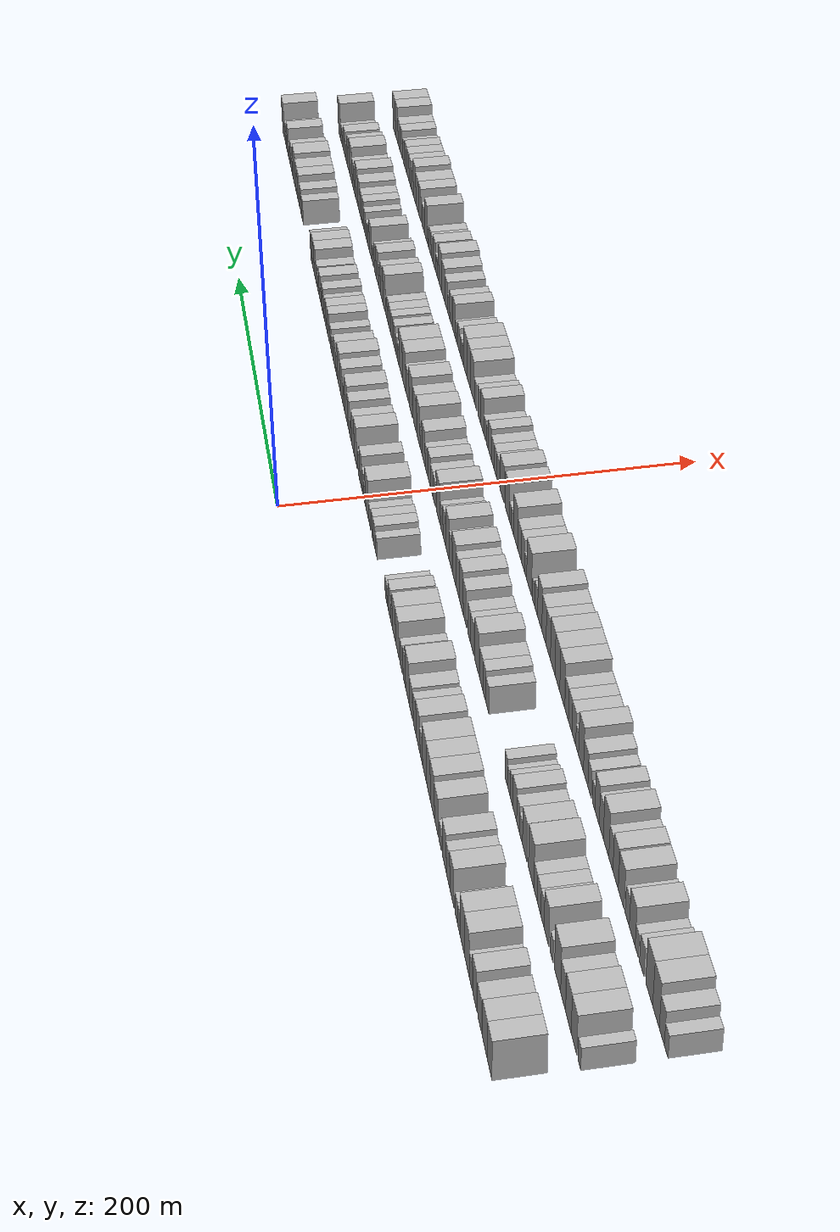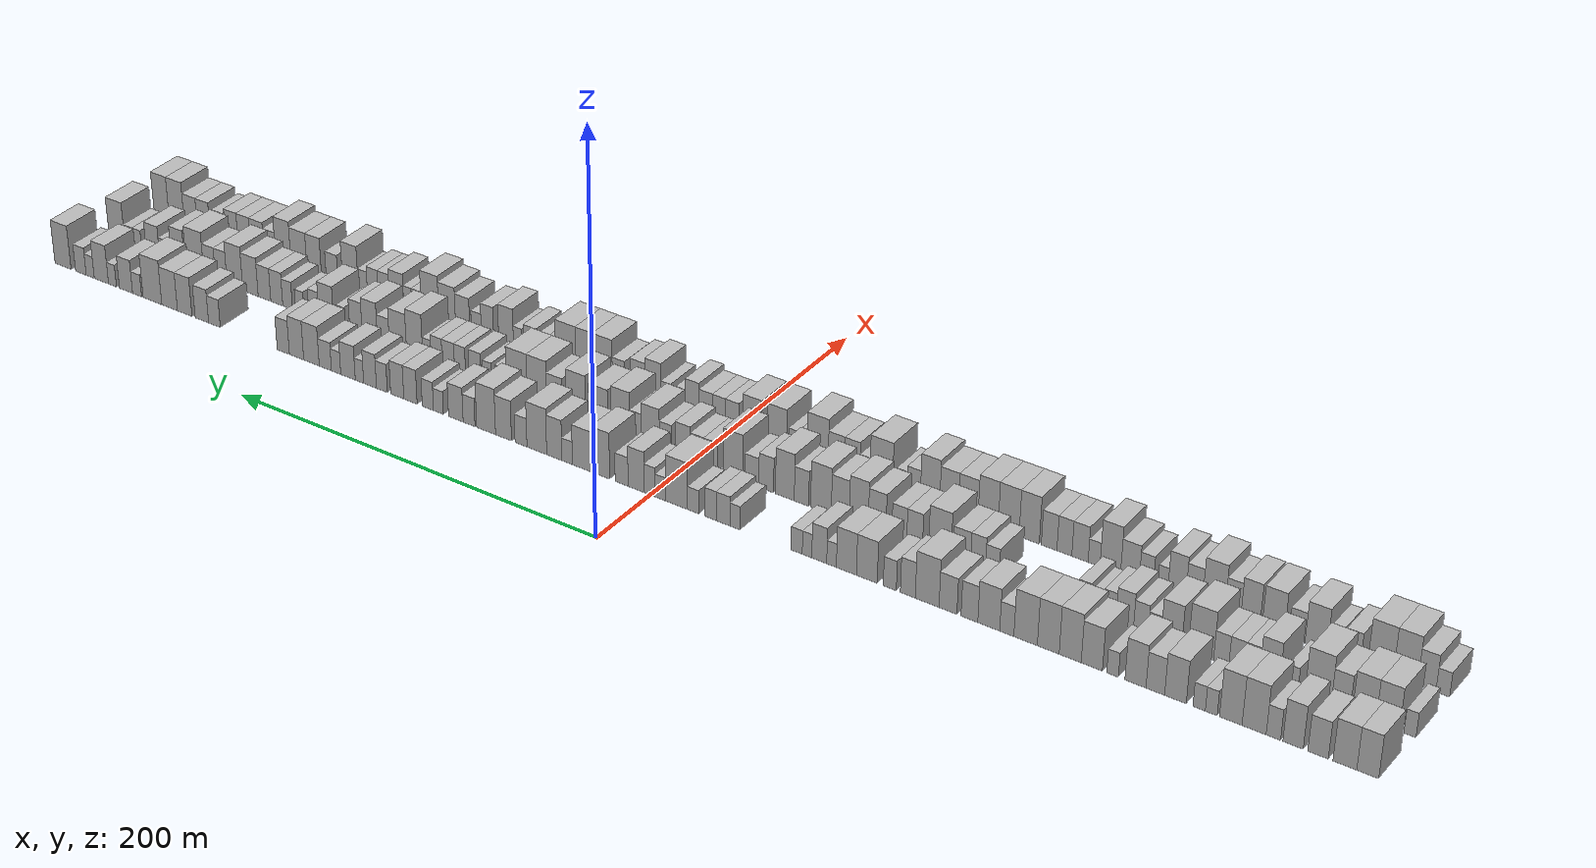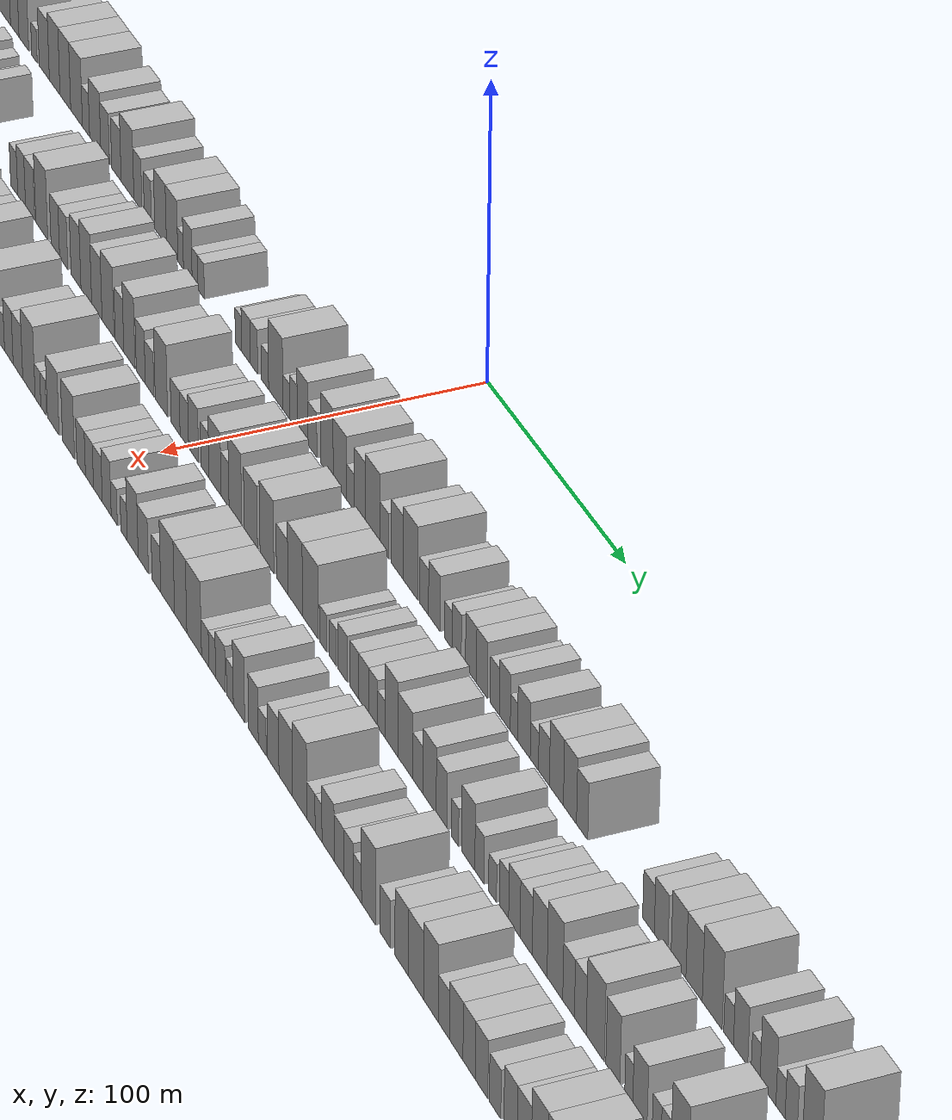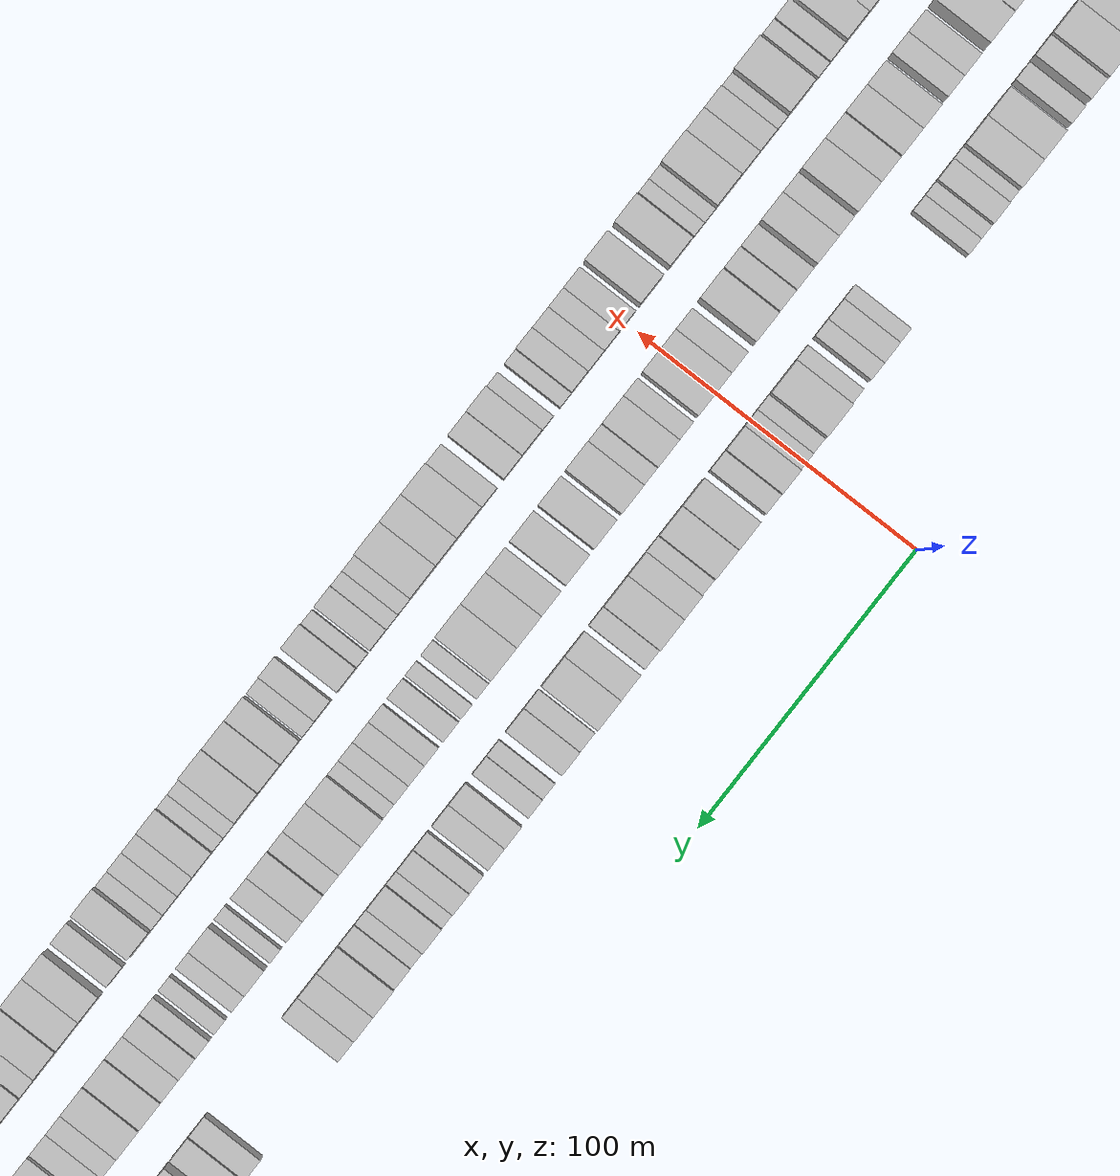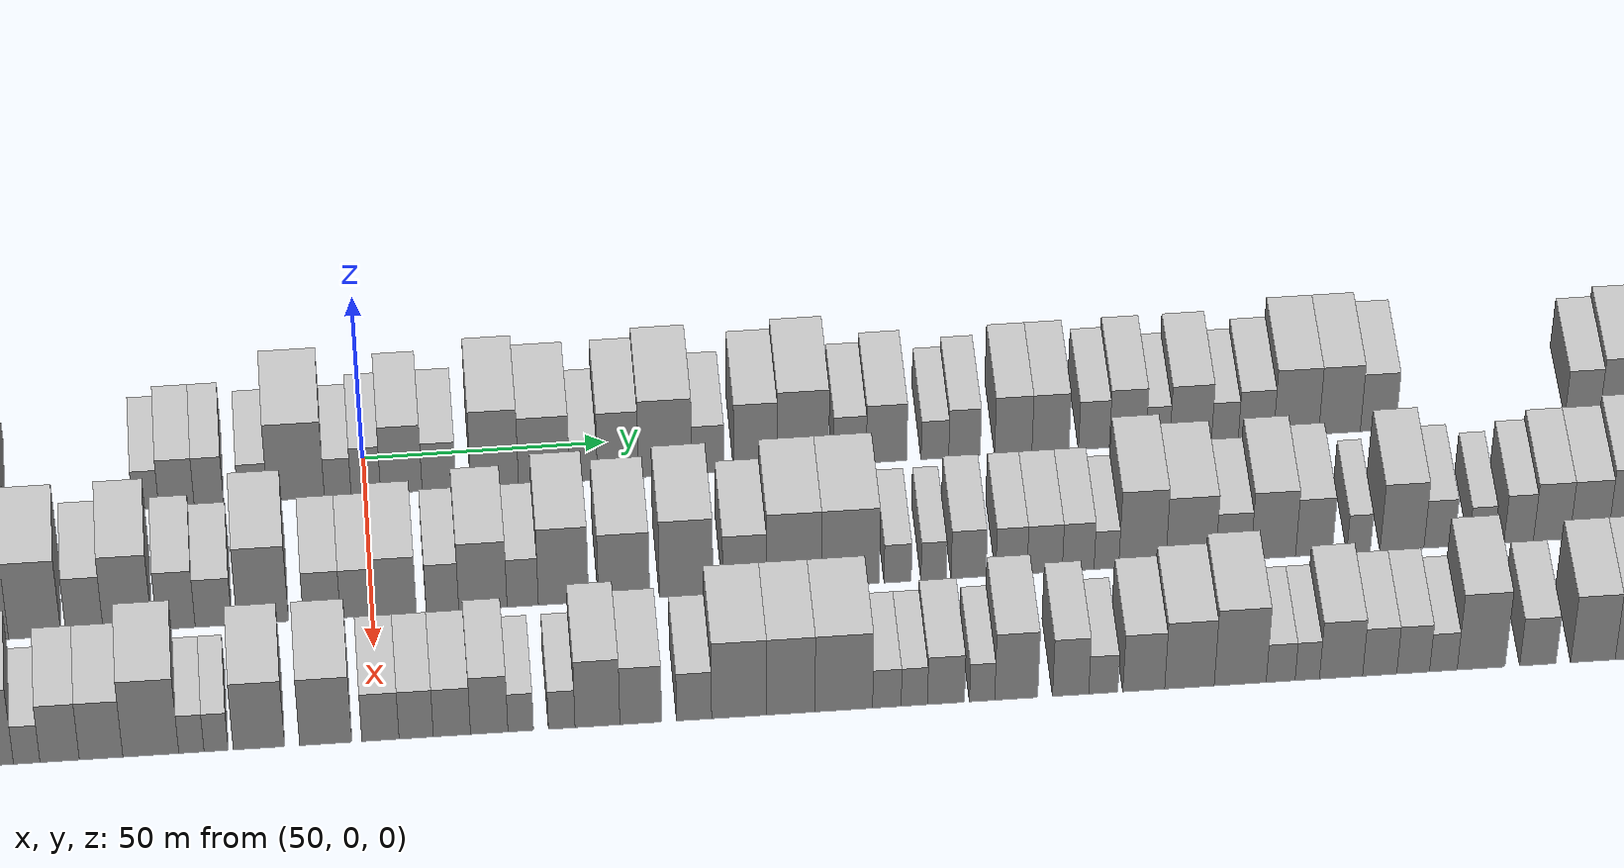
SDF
<sdf version="1.6">
 <world name="default">
  <scene>
   <sky><clouds><speed>12</speed></clouds></sky>
   <ambient>0.4 0.4 0.4 1</ambient>
   <background>0.7 0.7 0.7 1</background>
   <shadows>1</shadows>
  </scene>
  <gravity>0 0 -9.8066</gravity>
  <magnetic_field>6e-06 2.3e-05 -4.2e-05</magnetic_field>
  <physics default="0" name="default_physics" type="ode">
   <ode>
    <solver>
     <type>quick</type>
     <iters>10</iters>
     <sor>1.0</sor>
     <use_dynamic_moi_rescaling>0</use_dynamic_moi_rescaling>
    </solver>
    <constraints>
     <cfm>0</cfm>
     <erp>0.2</erp>
     <contact_max_correcting_vel>100</contact_max_correcting_vel>
     <contact_surface_layer>0.001</contact_surface_layer>
    </constraints>
   </ode>
   <max_step_size>0.004</max_step_size>
   <real_time_factor>1</real_time_factor>
   <real_time_update_rate>250</real_time_update_rate>
  </physics>
  <light name="sun" type="directional">
   <pose>0 0 10 0 0 0</pose>
   <diffuse>0.8 0.8 0.8 1</diffuse>
   <specular>0.2 0.2 0.2 1</specular>
   <attenuation>
    <range>1000</range>
    <constant>0.9</constant>
    <linear>0.01</linear>
    <quadratic>0.001</quadratic>
   </attenuation>
   <direction>-0.5 0.1 -0.9</direction>
  </light>
  <model name="building_1">
   <static>1</static>
   <pose>50.0000 -342.3423 0 0.000000 0.000000 0.000000</pose>
   <link name="link">
    <pose>0 0 10.50 0 0 0</pose>
    <collision name="collision"><geometry><box><size>20.0000 9.3154 21.0000</size></box></geometry></collision>
    <visual name="visual">
     <cast_shadows>0</cast_shadows>
     <geometry><box><size>20.0000 9.3154 21.0000</size></box></geometry>
     <material>
      <script>
       <uri>model://HANNAS_wall/materials/scripts</uri>
       <uri>model://HANNAS_wall/materials/textures</uri>
       <name>vrc/HANNAS_wall</name>
      </script>
     </material>
    </visual>
   </link>
  </model>
  <model name="building_2">
   <static>1</static>
   <pose>50.0000 -332.5979 0 0.000000 0.000000 0.000000</pose>
   <link name="link">
    <pose>0 0 10.50 0 0 0</pose>
    <collision name="collision"><geometry><box><size>20.0000 10.1734 21.0000</size></box></geometry></collision>
    <visual name="visual">
     <cast_shadows>0</cast_shadows>
     <geometry><box><size>20.0000 10.1734 21.0000</size></box></geometry>
     <material>
      <script>
       <uri>model://HANNAS_wall/materials/scripts</uri>
       <uri>model://HANNAS_wall/materials/textures</uri>
       <name>vrc/HANNAS_wall</name>
      </script>
     </material>
    </visual>
   </link>
  </model>
  <model name="building_3">
   <static>1</static>
   <pose>50.0000 -321.1037 0 0.000000 0.000000 0.000000</pose>
   <link name="link">
    <pose>0 0 9.00 0 0 0</pose>
    <collision name="collision"><geometry><box><size>20.0000 8.8150 18.0000</size></box></geometry></collision>
    <visual name="visual">
     <cast_shadows>0</cast_shadows>
     <geometry><box><size>20.0000 8.8150 18.0000</size></box></geometry>
     <material>
      <script>
       <uri>model://HANNAS_wall/materials/scripts</uri>
       <uri>model://HANNAS_wall/materials/textures</uri>
       <name>vrc/HANNAS_wall</name>
      </script>
     </material>
    </visual>
   </link>
  </model>
  <model name="building_4">
   <static>1</static>
   <pose>50.0000 -310.2756 0 0.000000 0.000000 0.000000</pose>
   <link name="link">
    <pose>0 0 10.50 0 0 0</pose>
    <collision name="collision"><geometry><box><size>20.0000 8.8411 21.0000</size></box></geometry></collision>
    <visual name="visual">
     <cast_shadows>0</cast_shadows>
     <geometry><box><size>20.0000 8.8411 21.0000</size></box></geometry>
     <material>
      <script>
       <uri>model://HANNAS_wall/materials/scripts</uri>
       <uri>model://HANNAS_wall/materials/textures</uri>
       <name>vrc/HANNAS_wall</name>
      </script>
     </material>
    </visual>
   </link>
  </model>
  <model name="building_5">
   <static>1</static>
   <pose>50.0000 -301.7045 0 0.000000 0.000000 0.000000</pose>
   <link name="link">
    <pose>0 0 7.50 0 0 0</pose>
    <collision name="collision"><geometry><box><size>20.0000 6.3011 15.0000</size></box></geometry></collision>
    <visual name="visual">
     <cast_shadows>0</cast_shadows>
     <geometry><box><size>20.0000 6.3011 15.0000</size></box></geometry>
     <material>
      <script>
       <uri>model://HANNAS_wall/materials/scripts</uri>
       <uri>model://HANNAS_wall/materials/textures</uri>
       <name>vrc/HANNAS_wall</name>
      </script>
     </material>
    </visual>
   </link>
  </model>
  <model name="building_6">
   <static>1</static>
   <pose>50.0000 -293.2562 0 0.000000 0.000000 0.000000</pose>
   <link name="link">
    <pose>0 0 12.00 0 0 0</pose>
    <collision name="collision"><geometry><box><size>20.0000 10.5956 24.0000</size></box></geometry></collision>
    <visual name="visual">
     <cast_shadows>0</cast_shadows>
     <geometry><box><size>20.0000 10.5956 24.0000</size></box></geometry>
     <material>
      <script>
       <uri>model://HANNAS_wall/materials/scripts</uri>
       <uri>model://HANNAS_wall/materials/textures</uri>
       <name>vrc/HANNAS_wall</name>
      </script>
     </material>
    </visual>
   </link>
  </model>
  <model name="building_7">
   <static>1</static>
   <pose>50.0000 -282.9576 0 0.000000 0.000000 0.000000</pose>
   <link name="link">
    <pose>0 0 12.00 0 0 0</pose>
    <collision name="collision"><geometry><box><size>20.0000 10.0018 24.0000</size></box></geometry></collision>
    <visual name="visual">
     <cast_shadows>0</cast_shadows>
     <geometry><box><size>20.0000 10.0018 24.0000</size></box></geometry>
     <material>
      <script>
       <uri>model://HANNAS_wall/materials/scripts</uri>
       <uri>model://HANNAS_wall/materials/textures</uri>
       <name>vrc/HANNAS_wall</name>
      </script>
     </material>
    </visual>
   </link>
  </model>
  <model name="building_8">
   <static>1</static>
   <pose>50.0000 -274.3203 0 0.000000 0.000000 0.000000</pose>
   <link name="link">
    <pose>0 0 6.00 0 0 0</pose>
    <collision name="collision"><geometry><box><size>20.0000 5.2728 12.0000</size></box></geometry></collision>
    <visual name="visual">
     <cast_shadows>0</cast_shadows>
     <geometry><box><size>20.0000 5.2728 12.0000</size></box></geometry>
     <material>
      <script>
       <uri>model://HANNAS_wall/materials/scripts</uri>
       <uri>model://HANNAS_wall/materials/textures</uri>
       <name>vrc/HANNAS_wall</name>
      </script>
     </material>
    </visual>
   </link>
  </model>
  <model name="building_9">
   <static>1</static>
   <pose>50.0000 -268.9081 0 0.000000 0.000000 0.000000</pose>
   <link name="link">
    <pose>0 0 6.00 0 0 0</pose>
    <collision name="collision"><geometry><box><size>20.0000 5.5516 12.0000</size></box></geometry></collision>
    <visual name="visual">
     <cast_shadows>0</cast_shadows>
     <geometry><box><size>20.0000 5.5516 12.0000</size></box></geometry>
     <material>
      <script>
       <uri>model://HANNAS_wall/materials/scripts</uri>
       <uri>model://HANNAS_wall/materials/textures</uri>
       <name>vrc/HANNAS_wall</name>
      </script>
     </material>
    </visual>
   </link>
  </model>
  <model name="building_10">
   <static>1</static>
   <pose>50.0000 -258.2499 0 0.000000 0.000000 0.000000</pose>
   <link name="link">
    <pose>0 0 10.50 0 0 0</pose>
    <collision name="collision"><geometry><box><size>20.0000 9.7648 21.0000</size></box></geometry></collision>
    <visual name="visual">
     <cast_shadows>0</cast_shadows>
     <geometry><box><size>20.0000 9.7648 21.0000</size></box></geometry>
     <material>
      <script>
       <uri>model://HANNAS_wall/materials/scripts</uri>
       <uri>model://HANNAS_wall/materials/textures</uri>
       <name>vrc/HANNAS_wall</name>
      </script>
     </material>
    </visual>
   </link>
  </model>
  <model name="building_11">
   <static>1</static>
   <pose>50.0000 -249.1407 0 0.000000 0.000000 0.000000</pose>
   <link name="link">
    <pose>0 0 9.00 0 0 0</pose>
    <collision name="collision"><geometry><box><size>20.0000 8.4536 18.0000</size></box></geometry></collision>
    <visual name="visual">
     <cast_shadows>0</cast_shadows>
     <geometry><box><size>20.0000 8.4536 18.0000</size></box></geometry>
     <material>
      <script>
       <uri>model://HANNAS_wall/materials/scripts</uri>
       <uri>model://HANNAS_wall/materials/textures</uri>
       <name>vrc/HANNAS_wall</name>
      </script>
     </material>
    </visual>
   </link>
  </model>
  <model name="building_12">
   <static>1</static>
   <pose>50.0000 -240.1204 0 0.000000 0.000000 0.000000</pose>
   <link name="link">
    <pose>0 0 10.50 0 0 0</pose>
    <collision name="collision"><geometry><box><size>20.0000 9.5869 21.0000</size></box></geometry></collision>
    <visual name="visual">
     <cast_shadows>0</cast_shadows>
     <geometry><box><size>20.0000 9.5869 21.0000</size></box></geometry>
     <material>
      <script>
       <uri>model://HANNAS_wall/materials/scripts</uri>
       <uri>model://HANNAS_wall/materials/textures</uri>
       <name>vrc/HANNAS_wall</name>
      </script>
     </material>
    </visual>
   </link>
  </model>
  <model name="building_13">
   <static>1</static>
   <pose>50.0000 -229.6478 0 0.000000 0.000000 0.000000</pose>
   <link name="link">
    <pose>0 0 6.00 0 0 0</pose>
    <collision name="collision"><geometry><box><size>20.0000 5.3583 12.0000</size></box></geometry></collision>
    <visual name="visual">
     <cast_shadows>0</cast_shadows>
     <geometry><box><size>20.0000 5.3583 12.0000</size></box></geometry>
     <material>
      <script>
       <uri>model://HANNAS_wall/materials/scripts</uri>
       <uri>model://HANNAS_wall/materials/textures</uri>
       <name>vrc/HANNAS_wall</name>
      </script>
     </material>
    </visual>
   </link>
  </model>
  <model name="building_14">
   <static>1</static>
   <pose>50.0000 -220.0654 0 0.000000 0.000000 0.000000</pose>
   <link name="link">
    <pose>0 0 10.50 0 0 0</pose>
    <collision name="collision"><geometry><box><size>20.0000 9.8064 21.0000</size></box></geometry></collision>
    <visual name="visual">
     <cast_shadows>0</cast_shadows>
     <geometry><box><size>20.0000 9.8064 21.0000</size></box></geometry>
     <material>
      <script>
       <uri>model://HANNAS_wall/materials/scripts</uri>
       <uri>model://HANNAS_wall/materials/textures</uri>
       <name>vrc/HANNAS_wall</name>
      </script>
     </material>
    </visual>
   </link>
  </model>
  <model name="building_15">
   <static>1</static>
   <pose>50.0000 -210.0278 0 0.000000 0.000000 0.000000</pose>
   <link name="link">
    <pose>0 0 12.00 0 0 0</pose>
    <collision name="collision"><geometry><box><size>20.0000 10.2688 24.0000</size></box></geometry></collision>
    <visual name="visual">
     <cast_shadows>0</cast_shadows>
     <geometry><box><size>20.0000 10.2688 24.0000</size></box></geometry>
     <material>
      <script>
       <uri>model://HANNAS_wall/materials/scripts</uri>
       <uri>model://HANNAS_wall/materials/textures</uri>
       <name>vrc/HANNAS_wall</name>
      </script>
     </material>
    </visual>
   </link>
  </model>
  <model name="building_16">
   <static>1</static>
   <pose>50.0000 -199.7752 0 0.000000 0.000000 0.000000</pose>
   <link name="link">
    <pose>0 0 12.00 0 0 0</pose>
    <collision name="collision"><geometry><box><size>20.0000 10.2365 24.0000</size></box></geometry></collision>
    <visual name="visual">
     <cast_shadows>0</cast_shadows>
     <geometry><box><size>20.0000 10.2365 24.0000</size></box></geometry>
     <material>
      <script>
       <uri>model://HANNAS_wall/materials/scripts</uri>
       <uri>model://HANNAS_wall/materials/textures</uri>
       <name>vrc/HANNAS_wall</name>
      </script>
     </material>
    </visual>
   </link>
  </model>
  <model name="building_17">
   <static>1</static>
   <pose>50.0000 -189.1003 0 0.000000 0.000000 0.000000</pose>
   <link name="link">
    <pose>0 0 12.00 0 0 0</pose>
    <collision name="collision"><geometry><box><size>20.0000 11.1133 24.0000</size></box></geometry></collision>
    <visual name="visual">
     <cast_shadows>0</cast_shadows>
     <geometry><box><size>20.0000 11.1133 24.0000</size></box></geometry>
     <material>
      <script>
       <uri>model://HANNAS_wall/materials/scripts</uri>
       <uri>model://HANNAS_wall/materials/textures</uri>
       <name>vrc/HANNAS_wall</name>
      </script>
     </material>
    </visual>
   </link>
  </model>
  <model name="building_18">
   <static>1</static>
   <pose>50.0000 -180.1797 0 0.000000 0.000000 0.000000</pose>
   <link name="link">
    <pose>0 0 7.50 0 0 0</pose>
    <collision name="collision"><geometry><box><size>20.0000 6.7280 15.0000</size></box></geometry></collision>
    <visual name="visual">
     <cast_shadows>0</cast_shadows>
     <geometry><box><size>20.0000 6.7280 15.0000</size></box></geometry>
     <material>
      <script>
       <uri>model://HANNAS_wall/materials/scripts</uri>
       <uri>model://HANNAS_wall/materials/textures</uri>
       <name>vrc/HANNAS_wall</name>
      </script>
     </material>
    </visual>
   </link>
  </model>
  <model name="building_19">
   <static>1</static>
   <pose>50.0000 -171.5778 0 0.000000 0.000000 0.000000</pose>
   <link name="link">
    <pose>0 0 10.50 0 0 0</pose>
    <collision name="collision"><geometry><box><size>20.0000 10.4758 21.0000</size></box></geometry></collision>
    <visual name="visual">
     <cast_shadows>0</cast_shadows>
     <geometry><box><size>20.0000 10.4758 21.0000</size></box></geometry>
     <material>
      <script>
       <uri>model://HANNAS_wall/materials/scripts</uri>
       <uri>model://HANNAS_wall/materials/textures</uri>
       <name>vrc/HANNAS_wall</name>
      </script>
     </material>
    </visual>
   </link>
  </model>
  <model name="building_20">
   <static>1</static>
   <pose>50.0000 -162.3032 0 0.000000 0.000000 0.000000</pose>
   <link name="link">
    <pose>0 0 9.00 0 0 0</pose>
    <collision name="collision"><geometry><box><size>20.0000 8.0733 18.0000</size></box></geometry></collision>
    <visual name="visual">
     <cast_shadows>0</cast_shadows>
     <geometry><box><size>20.0000 8.0733 18.0000</size></box></geometry>
     <material>
      <script>
       <uri>model://HANNAS_wall/materials/scripts</uri>
       <uri>model://HANNAS_wall/materials/textures</uri>
       <name>vrc/HANNAS_wall</name>
      </script>
     </material>
    </visual>
   </link>
  </model>
  <model name="building_21">
   <static>1</static>
   <pose>50.0000 -151.9376 0 0.000000 0.000000 0.000000</pose>
   <link name="link">
    <pose>0 0 9.00 0 0 0</pose>
    <collision name="collision"><geometry><box><size>20.0000 8.6579 18.0000</size></box></geometry></collision>
    <visual name="visual">
     <cast_shadows>0</cast_shadows>
     <geometry><box><size>20.0000 8.6579 18.0000</size></box></geometry>
     <material>
      <script>
       <uri>model://HANNAS_wall/materials/scripts</uri>
       <uri>model://HANNAS_wall/materials/textures</uri>
       <name>vrc/HANNAS_wall</name>
      </script>
     </material>
    </visual>
   </link>
  </model>
  <model name="building_22">
   <static>1</static>
   <pose>50.0000 -141.8057 0 0.000000 0.000000 0.000000</pose>
   <link name="link">
    <pose>0 0 12.00 0 0 0</pose>
    <collision name="collision"><geometry><box><size>20.0000 11.6058 24.0000</size></box></geometry></collision>
    <visual name="visual">
     <cast_shadows>0</cast_shadows>
     <geometry><box><size>20.0000 11.6058 24.0000</size></box></geometry>
     <material>
      <script>
       <uri>model://HANNAS_wall/materials/scripts</uri>
       <uri>model://HANNAS_wall/materials/textures</uri>
       <name>vrc/HANNAS_wall</name>
      </script>
     </material>
    </visual>
   </link>
  </model>
  <model name="building_23">
   <static>1</static>
   <pose>50.0000 -132.3455 0 0.000000 0.000000 0.000000</pose>
   <link name="link">
    <pose>0 0 9.00 0 0 0</pose>
    <collision name="collision"><geometry><box><size>20.0000 7.3147 18.0000</size></box></geometry></collision>
    <visual name="visual">
     <cast_shadows>0</cast_shadows>
     <geometry><box><size>20.0000 7.3147 18.0000</size></box></geometry>
     <material>
      <script>
       <uri>model://HANNAS_wall/materials/scripts</uri>
       <uri>model://HANNAS_wall/materials/textures</uri>
       <name>vrc/HANNAS_wall</name>
      </script>
     </material>
    </visual>
   </link>
  </model>
  <model name="building_24">
   <static>1</static>
   <pose>50.0000 -123.4664 0 0.000000 0.000000 0.000000</pose>
   <link name="link">
    <pose>0 0 7.50 0 0 0</pose>
    <collision name="collision"><geometry><box><size>20.0000 6.4434 15.0000</size></box></geometry></collision>
    <visual name="visual">
     <cast_shadows>0</cast_shadows>
     <geometry><box><size>20.0000 6.4434 15.0000</size></box></geometry>
     <material>
      <script>
       <uri>model://HANNAS_wall/materials/scripts</uri>
       <uri>model://HANNAS_wall/materials/textures</uri>
       <name>vrc/HANNAS_wall</name>
      </script>
     </material>
    </visual>
   </link>
  </model>
  <model name="building_25">
   <static>1</static>
   <pose>50.0000 -112.0705 0 0.000000 0.000000 0.000000</pose>
   <link name="link">
    <pose>0 0 10.50 0 0 0</pose>
    <collision name="collision"><geometry><box><size>20.0000 10.3483 21.0000</size></box></geometry></collision>
    <visual name="visual">
     <cast_shadows>0</cast_shadows>
     <geometry><box><size>20.0000 10.3483 21.0000</size></box></geometry>
     <material>
      <script>
       <uri>model://HANNAS_wall/materials/scripts</uri>
       <uri>model://HANNAS_wall/materials/textures</uri>
       <name>vrc/HANNAS_wall</name>
      </script>
     </material>
    </visual>
   </link>
  </model>
  <model name="building_26">
   <static>1</static>
   <pose>50.0000 -101.8684 0 0.000000 0.000000 0.000000</pose>
   <link name="link">
    <pose>0 0 10.50 0 0 0</pose>
    <collision name="collision"><geometry><box><size>20.0000 10.0559 21.0000</size></box></geometry></collision>
    <visual name="visual">
     <cast_shadows>0</cast_shadows>
     <geometry><box><size>20.0000 10.0559 21.0000</size></box></geometry>
     <material>
      <script>
       <uri>model://HANNAS_wall/materials/scripts</uri>
       <uri>model://HANNAS_wall/materials/textures</uri>
       <name>vrc/HANNAS_wall</name>
      </script>
     </material>
    </visual>
   </link>
  </model>
  <model name="building_27">
   <static>1</static>
   <pose>50.0000 -94.3992 0 0.000000 0.000000 0.000000</pose>
   <link name="link">
    <pose>0 0 6.00 0 0 0</pose>
    <collision name="collision"><geometry><box><size>20.0000 4.8827 12.0000</size></box></geometry></collision>
    <visual name="visual">
     <cast_shadows>0</cast_shadows>
     <geometry><box><size>20.0000 4.8827 12.0000</size></box></geometry>
     <material>
      <script>
       <uri>model://HANNAS_wall/materials/scripts</uri>
       <uri>model://HANNAS_wall/materials/textures</uri>
       <name>vrc/HANNAS_wall</name>
      </script>
     </material>
    </visual>
   </link>
  </model>
  <model name="building_28">
   <static>1</static>
   <pose>50.0000 -88.1962 0 0.000000 0.000000 0.000000</pose>
   <link name="link">
    <pose>0 0 9.00 0 0 0</pose>
    <collision name="collision"><geometry><box><size>20.0000 7.5232 18.0000</size></box></geometry></collision>
    <visual name="visual">
     <cast_shadows>0</cast_shadows>
     <geometry><box><size>20.0000 7.5232 18.0000</size></box></geometry>
     <material>
      <script>
       <uri>model://HANNAS_wall/materials/scripts</uri>
       <uri>model://HANNAS_wall/materials/textures</uri>
       <name>vrc/HANNAS_wall</name>
      </script>
     </material>
    </visual>
   </link>
  </model>
  <model name="building_29">
   <static>1</static>
   <pose>50.0000 -82.0063 0 0.000000 0.000000 0.000000</pose>
   <link name="link">
    <pose>0 0 6.00 0 0 0</pose>
    <collision name="collision"><geometry><box><size>20.0000 4.8566 12.0000</size></box></geometry></collision>
    <visual name="visual">
     <cast_shadows>0</cast_shadows>
     <geometry><box><size>20.0000 4.8566 12.0000</size></box></geometry>
     <material>
      <script>
       <uri>model://HANNAS_wall/materials/scripts</uri>
       <uri>model://HANNAS_wall/materials/textures</uri>
       <name>vrc/HANNAS_wall</name>
      </script>
     </material>
    </visual>
   </link>
  </model>
  <model name="building_30">
   <static>1</static>
   <pose>50.0000 -76.7317 0 0.000000 0.000000 0.000000</pose>
   <link name="link">
    <pose>0 0 6.00 0 0 0</pose>
    <collision name="collision"><geometry><box><size>20.0000 5.6926 12.0000</size></box></geometry></collision>
    <visual name="visual">
     <cast_shadows>0</cast_shadows>
     <geometry><box><size>20.0000 5.6926 12.0000</size></box></geometry>
     <material>
      <script>
       <uri>model://HANNAS_wall/materials/scripts</uri>
       <uri>model://HANNAS_wall/materials/textures</uri>
       <name>vrc/HANNAS_wall</name>
      </script>
     </material>
    </visual>
   </link>
  </model>
  <model name="building_31">
   <static>1</static>
   <pose>50.0000 -44.9944 0 0.000000 0.000000 0.000000</pose>
   <link name="link">
    <pose>0 0 6.00 0 0 0</pose>
    <collision name="collision"><geometry><box><size>20.0000 5.2606 12.0000</size></box></geometry></collision>
    <visual name="visual">
     <cast_shadows>0</cast_shadows>
     <geometry><box><size>20.0000 5.2606 12.0000</size></box></geometry>
     <material>
      <script>
       <uri>model://HANNAS_wall/materials/scripts</uri>
       <uri>model://HANNAS_wall/materials/textures</uri>
       <name>vrc/HANNAS_wall</name>
      </script>
     </material>
    </visual>
   </link>
  </model>
  <model name="building_32">
   <static>1</static>
   <pose>50.0000 -38.7265 0 0.000000 0.000000 0.000000</pose>
   <link name="link">
    <pose>0 0 7.50 0 0 0</pose>
    <collision name="collision"><geometry><box><size>20.0000 7.2752 15.0000</size></box></geometry></collision>
    <visual name="visual">
     <cast_shadows>0</cast_shadows>
     <geometry><box><size>20.0000 7.2752 15.0000</size></box></geometry>
     <material>
      <script>
       <uri>model://HANNAS_wall/materials/scripts</uri>
       <uri>model://HANNAS_wall/materials/textures</uri>
       <name>vrc/HANNAS_wall</name>
      </script>
     </material>
    </visual>
   </link>
  </model>
  <model name="building_33">
   <static>1</static>
   <pose>50.0000 -32.0536 0 0.000000 0.000000 0.000000</pose>
   <link name="link">
    <pose>0 0 7.50 0 0 0</pose>
    <collision name="collision"><geometry><box><size>20.0000 6.0708 15.0000</size></box></geometry></collision>
    <visual name="visual">
     <cast_shadows>0</cast_shadows>
     <geometry><box><size>20.0000 6.0708 15.0000</size></box></geometry>
     <material>
      <script>
       <uri>model://HANNAS_wall/materials/scripts</uri>
       <uri>model://HANNAS_wall/materials/textures</uri>
       <name>vrc/HANNAS_wall</name>
      </script>
     </material>
    </visual>
   </link>
  </model>
  <model name="building_34">
   <static>1</static>
   <pose>50.0000 -23.0330 0 0.000000 0.000000 0.000000</pose>
   <link name="link">
    <pose>0 0 6.00 0 0 0</pose>
    <collision name="collision"><geometry><box><size>20.0000 5.9702 12.0000</size></box></geometry></collision>
    <visual name="visual">
     <cast_shadows>0</cast_shadows>
     <geometry><box><size>20.0000 5.9702 12.0000</size></box></geometry>
     <material>
      <script>
       <uri>model://HANNAS_wall/materials/scripts</uri>
       <uri>model://HANNAS_wall/materials/textures</uri>
       <name>vrc/HANNAS_wall</name>
      </script>
     </material>
    </visual>
   </link>
  </model>
  <model name="building_35">
   <static>1</static>
   <pose>50.0000 -14.2006 0 0.000000 0.000000 0.000000</pose>
   <link name="link">
    <pose>0 0 12.00 0 0 0</pose>
    <collision name="collision"><geometry><box><size>20.0000 11.6945 24.0000</size></box></geometry></collision>
    <visual name="visual">
     <cast_shadows>0</cast_shadows>
     <geometry><box><size>20.0000 11.6945 24.0000</size></box></geometry>
     <material>
      <script>
       <uri>model://HANNAS_wall/materials/scripts</uri>
       <uri>model://HANNAS_wall/materials/textures</uri>
       <name>vrc/HANNAS_wall</name>
      </script>
     </material>
    </visual>
   </link>
  </model>
  <model name="building_36">
   <static>1</static>
   <pose>50.0000 -5.5982 0 0.000000 0.000000 0.000000</pose>
   <link name="link">
    <pose>0 0 6.00 0 0 0</pose>
    <collision name="collision"><geometry><box><size>20.0000 5.5104 12.0000</size></box></geometry></collision>
    <visual name="visual">
     <cast_shadows>0</cast_shadows>
     <geometry><box><size>20.0000 5.5104 12.0000</size></box></geometry>
     <material>
      <script>
       <uri>model://HANNAS_wall/materials/scripts</uri>
       <uri>model://HANNAS_wall/materials/textures</uri>
       <name>vrc/HANNAS_wall</name>
      </script>
     </material>
    </visual>
   </link>
  </model>
  <model name="building_37">
   <static>1</static>
   <pose>50.0000 0.1944 0 0.000000 0.000000 0.000000</pose>
   <link name="link">
    <pose>0 0 7.50 0 0 0</pose>
    <collision name="collision"><geometry><box><size>20.0000 6.0749 15.0000</size></box></geometry></collision>
    <visual name="visual">
     <cast_shadows>0</cast_shadows>
     <geometry><box><size>20.0000 6.0749 15.0000</size></box></geometry>
     <material>
      <script>
       <uri>model://HANNAS_wall/materials/scripts</uri>
       <uri>model://HANNAS_wall/materials/textures</uri>
       <name>vrc/HANNAS_wall</name>
      </script>
     </material>
    </visual>
   </link>
  </model>
  <model name="building_38">
   <static>1</static>
   <pose>50.0000 7.5005 0 0.000000 0.000000 0.000000</pose>
   <link name="link">
    <pose>0 0 10.50 0 0 0</pose>
    <collision name="collision"><geometry><box><size>20.0000 8.5372 21.0000</size></box></geometry></collision>
    <visual name="visual">
     <cast_shadows>0</cast_shadows>
     <geometry><box><size>20.0000 8.5372 21.0000</size></box></geometry>
     <material>
      <script>
       <uri>model://HANNAS_wall/materials/scripts</uri>
       <uri>model://HANNAS_wall/materials/textures</uri>
       <name>vrc/HANNAS_wall</name>
      </script>
     </material>
    </visual>
   </link>
  </model>
  <model name="building_39">
   <static>1</static>
   <pose>50.0000 15.2704 0 0.000000 0.000000 0.000000</pose>
   <link name="link">
    <pose>0 0 7.50 0 0 0</pose>
    <collision name="collision"><geometry><box><size>20.0000 7.0027 15.0000</size></box></geometry></collision>
    <visual name="visual">
     <cast_shadows>0</cast_shadows>
     <geometry><box><size>20.0000 7.0027 15.0000</size></box></geometry>
     <material>
      <script>
       <uri>model://HANNAS_wall/materials/scripts</uri>
       <uri>model://HANNAS_wall/materials/textures</uri>
       <name>vrc/HANNAS_wall</name>
      </script>
     </material>
    </visual>
   </link>
  </model>
  <model name="building_40">
   <static>1</static>
   <pose>50.0000 26.6961 0 0.000000 0.000000 0.000000</pose>
   <link name="link">
    <pose>0 0 12.00 0 0 0</pose>
    <collision name="collision"><geometry><box><size>20.0000 9.8487 24.0000</size></box></geometry></collision>
    <visual name="visual">
     <cast_shadows>0</cast_shadows>
     <geometry><box><size>20.0000 9.8487 24.0000</size></box></geometry>
     <material>
      <script>
       <uri>model://HANNAS_wall/materials/scripts</uri>
       <uri>model://HANNAS_wall/materials/textures</uri>
       <name>vrc/HANNAS_wall</name>
      </script>
     </material>
    </visual>
   </link>
  </model>
  <model name="building_41">
   <static>1</static>
   <pose>50.0000 36.8690 0 0.000000 0.000000 0.000000</pose>
   <link name="link">
    <pose>0 0 10.50 0 0 0</pose>
    <collision name="collision"><geometry><box><size>20.0000 10.4971 21.0000</size></box></geometry></collision>
    <visual name="visual">
     <cast_shadows>0</cast_shadows>
     <geometry><box><size>20.0000 10.4971 21.0000</size></box></geometry>
     <material>
      <script>
       <uri>model://HANNAS_wall/materials/scripts</uri>
       <uri>model://HANNAS_wall/materials/textures</uri>
       <name>vrc/HANNAS_wall</name>
      </script>
     </material>
    </visual>
   </link>
  </model>
  <model name="building_42">
   <static>1</static>
   <pose>50.0000 45.0022 0 0.000000 0.000000 0.000000</pose>
   <link name="link">
    <pose>0 0 6.00 0 0 0</pose>
    <collision name="collision"><geometry><box><size>20.0000 5.7693 12.0000</size></box></geometry></collision>
    <visual name="visual">
     <cast_shadows>0</cast_shadows>
     <geometry><box><size>20.0000 5.7693 12.0000</size></box></geometry>
     <material>
      <script>
       <uri>model://HANNAS_wall/materials/scripts</uri>
       <uri>model://HANNAS_wall/materials/textures</uri>
       <name>vrc/HANNAS_wall</name>
      </script>
     </material>
    </visual>
   </link>
  </model>
  <model name="building_43">
   <static>1</static>
   <pose>50.0000 52.1193 0 0.000000 0.000000 0.000000</pose>
   <link name="link">
    <pose>0 0 10.50 0 0 0</pose>
    <collision name="collision"><geometry><box><size>20.0000 8.4649 21.0000</size></box></geometry></collision>
    <visual name="visual">
     <cast_shadows>0</cast_shadows>
     <geometry><box><size>20.0000 8.4649 21.0000</size></box></geometry>
     <material>
      <script>
       <uri>model://HANNAS_wall/materials/scripts</uri>
       <uri>model://HANNAS_wall/materials/textures</uri>
       <name>vrc/HANNAS_wall</name>
      </script>
     </material>
    </visual>
   </link>
  </model>
  <model name="building_44">
   <static>1</static>
   <pose>50.0000 61.8572 0 0.000000 0.000000 0.000000</pose>
   <link name="link">
    <pose>0 0 12.00 0 0 0</pose>
    <collision name="collision"><geometry><box><size>20.0000 11.0109 24.0000</size></box></geometry></collision>
    <visual name="visual">
     <cast_shadows>0</cast_shadows>
     <geometry><box><size>20.0000 11.0109 24.0000</size></box></geometry>
     <material>
      <script>
       <uri>model://HANNAS_wall/materials/scripts</uri>
       <uri>model://HANNAS_wall/materials/textures</uri>
       <name>vrc/HANNAS_wall</name>
      </script>
     </material>
    </visual>
   </link>
  </model>
  <model name="building_45">
   <static>1</static>
   <pose>50.0000 70.7023 0 0.000000 0.000000 0.000000</pose>
   <link name="link">
    <pose>0 0 7.50 0 0 0</pose>
    <collision name="collision"><geometry><box><size>20.0000 6.6793 15.0000</size></box></geometry></collision>
    <visual name="visual">
     <cast_shadows>0</cast_shadows>
     <geometry><box><size>20.0000 6.6793 15.0000</size></box></geometry>
     <material>
      <script>
       <uri>model://HANNAS_wall/materials/scripts</uri>
       <uri>model://HANNAS_wall/materials/textures</uri>
       <name>vrc/HANNAS_wall</name>
      </script>
     </material>
    </visual>
   </link>
  </model>
  <model name="building_46">
   <static>1</static>
   <pose>50.0000 80.5464 0 0.000000 0.000000 0.000000</pose>
   <link name="link">
    <pose>0 0 10.50 0 0 0</pose>
    <collision name="collision"><geometry><box><size>20.0000 9.0089 21.0000</size></box></geometry></collision>
    <visual name="visual">
     <cast_shadows>0</cast_shadows>
     <geometry><box><size>20.0000 9.0089 21.0000</size></box></geometry>
     <material>
      <script>
       <uri>model://HANNAS_wall/materials/scripts</uri>
       <uri>model://HANNAS_wall/materials/textures</uri>
       <name>vrc/HANNAS_wall</name>
      </script>
     </material>
    </visual>
   </link>
  </model>
  <model name="building_47">
   <static>1</static>
   <pose>50.0000 90.3913 0 0.000000 0.000000 0.000000</pose>
   <link name="link">
    <pose>0 0 12.00 0 0 0</pose>
    <collision name="collision"><geometry><box><size>20.0000 10.6811 24.0000</size></box></geometry></collision>
    <visual name="visual">
     <cast_shadows>0</cast_shadows>
     <geometry><box><size>20.0000 10.6811 24.0000</size></box></geometry>
     <material>
      <script>
       <uri>model://HANNAS_wall/materials/scripts</uri>
       <uri>model://HANNAS_wall/materials/textures</uri>
       <name>vrc/HANNAS_wall</name>
      </script>
     </material>
    </visual>
   </link>
  </model>
  <model name="building_48">
   <static>1</static>
   <pose>50.0000 100.1122 0 0.000000 0.000000 0.000000</pose>
   <link name="link">
    <pose>0 0 7.50 0 0 0</pose>
    <collision name="collision"><geometry><box><size>20.0000 6.7606 15.0000</size></box></geometry></collision>
    <visual name="visual">
     <cast_shadows>0</cast_shadows>
     <geometry><box><size>20.0000 6.7606 15.0000</size></box></geometry>
     <material>
      <script>
       <uri>model://HANNAS_wall/materials/scripts</uri>
       <uri>model://HANNAS_wall/materials/textures</uri>
       <name>vrc/HANNAS_wall</name>
      </script>
     </material>
    </visual>
   </link>
  </model>
  <model name="building_49">
   <static>1</static>
   <pose>50.0000 107.6682 0 0.000000 0.000000 0.000000</pose>
   <link name="link">
    <pose>0 0 9.00 0 0 0</pose>
    <collision name="collision"><geometry><box><size>20.0000 8.3515 18.0000</size></box></geometry></collision>
    <visual name="visual">
     <cast_shadows>0</cast_shadows>
     <geometry><box><size>20.0000 8.3515 18.0000</size></box></geometry>
     <material>
      <script>
       <uri>model://HANNAS_wall/materials/scripts</uri>
       <uri>model://HANNAS_wall/materials/textures</uri>
       <name>vrc/HANNAS_wall</name>
      </script>
     </material>
    </visual>
   </link>
  </model>
  <model name="building_50">
   <static>1</static>
   <pose>50.0000 117.6989 0 0.000000 0.000000 0.000000</pose>
   <link name="link">
    <pose>0 0 6.00 0 0 0</pose>
    <collision name="collision"><geometry><box><size>20.0000 5.7099 12.0000</size></box></geometry></collision>
    <visual name="visual">
     <cast_shadows>0</cast_shadows>
     <geometry><box><size>20.0000 5.7099 12.0000</size></box></geometry>
     <material>
      <script>
       <uri>model://HANNAS_wall/materials/scripts</uri>
       <uri>model://HANNAS_wall/materials/textures</uri>
       <name>vrc/HANNAS_wall</name>
      </script>
     </material>
    </visual>
   </link>
  </model>
  <model name="building_51">
   <static>1</static>
   <pose>50.0000 123.8162 0 0.000000 0.000000 0.000000</pose>
   <link name="link">
    <pose>0 0 7.50 0 0 0</pose>
    <collision name="collision"><geometry><box><size>20.0000 6.5247 15.0000</size></box></geometry></collision>
    <visual name="visual">
     <cast_shadows>0</cast_shadows>
     <geometry><box><size>20.0000 6.5247 15.0000</size></box></geometry>
     <material>
      <script>
       <uri>model://HANNAS_wall/materials/scripts</uri>
       <uri>model://HANNAS_wall/materials/textures</uri>
       <name>vrc/HANNAS_wall</name>
      </script>
     </material>
    </visual>
   </link>
  </model>
  <model name="building_52">
   <static>1</static>
   <pose>50.0000 133.9477 0 0.000000 0.000000 0.000000</pose>
   <link name="link">
    <pose>0 0 9.00 0 0 0</pose>
    <collision name="collision"><geometry><box><size>20.0000 7.7381 18.0000</size></box></geometry></collision>
    <visual name="visual">
     <cast_shadows>0</cast_shadows>
     <geometry><box><size>20.0000 7.7381 18.0000</size></box></geometry>
     <material>
      <script>
       <uri>model://HANNAS_wall/materials/scripts</uri>
       <uri>model://HANNAS_wall/materials/textures</uri>
       <name>vrc/HANNAS_wall</name>
      </script>
     </material>
    </visual>
   </link>
  </model>
  <model name="building_53">
   <static>1</static>
   <pose>50.0000 141.6586 0 0.000000 0.000000 0.000000</pose>
   <link name="link">
    <pose>0 0 9.00 0 0 0</pose>
    <collision name="collision"><geometry><box><size>20.0000 7.6837 18.0000</size></box></geometry></collision>
    <visual name="visual">
     <cast_shadows>0</cast_shadows>
     <geometry><box><size>20.0000 7.6837 18.0000</size></box></geometry>
     <material>
      <script>
       <uri>model://HANNAS_wall/materials/scripts</uri>
       <uri>model://HANNAS_wall/materials/textures</uri>
       <name>vrc/HANNAS_wall</name>
      </script>
     </material>
    </visual>
   </link>
  </model>
  <model name="building_54">
   <static>1</static>
   <pose>50.0000 150.6986 0 0.000000 0.000000 0.000000</pose>
   <link name="link">
    <pose>0 0 7.50 0 0 0</pose>
    <collision name="collision"><geometry><box><size>20.0000 6.3965 15.0000</size></box></geometry></collision>
    <visual name="visual">
     <cast_shadows>0</cast_shadows>
     <geometry><box><size>20.0000 6.3965 15.0000</size></box></geometry>
     <material>
      <script>
       <uri>model://HANNAS_wall/materials/scripts</uri>
       <uri>model://HANNAS_wall/materials/textures</uri>
       <name>vrc/HANNAS_wall</name>
      </script>
     </material>
    </visual>
   </link>
  </model>
  <model name="building_55">
   <static>1</static>
   <pose>50.0000 157.6877 0 0.000000 0.000000 0.000000</pose>
   <link name="link">
    <pose>0 0 9.00 0 0 0</pose>
    <collision name="collision"><geometry><box><size>20.0000 7.5816 18.0000</size></box></geometry></collision>
    <visual name="visual">
     <cast_shadows>0</cast_shadows>
     <geometry><box><size>20.0000 7.5816 18.0000</size></box></geometry>
     <material>
      <script>
       <uri>model://HANNAS_wall/materials/scripts</uri>
       <uri>model://HANNAS_wall/materials/textures</uri>
       <name>vrc/HANNAS_wall</name>
      </script>
     </material>
    </visual>
   </link>
  </model>
  <model name="building_56">
   <static>1</static>
   <pose>50.0000 163.9735 0 0.000000 0.000000 0.000000</pose>
   <link name="link">
    <pose>0 0 6.00 0 0 0</pose>
    <collision name="collision"><geometry><box><size>20.0000 4.9901 12.0000</size></box></geometry></collision>
    <visual name="visual">
     <cast_shadows>0</cast_shadows>
     <geometry><box><size>20.0000 4.9901 12.0000</size></box></geometry>
     <material>
      <script>
       <uri>model://HANNAS_wall/materials/scripts</uri>
       <uri>model://HANNAS_wall/materials/textures</uri>
       <name>vrc/HANNAS_wall</name>
      </script>
     </material>
    </visual>
   </link>
  </model>
  <model name="building_57">
   <static>1</static>
   <pose>50.0000 170.8108 0 0.000000 0.000000 0.000000</pose>
   <link name="link">
    <pose>0 0 9.00 0 0 0</pose>
    <collision name="collision"><geometry><box><size>20.0000 8.6844 18.0000</size></box></geometry></collision>
    <visual name="visual">
     <cast_shadows>0</cast_shadows>
     <geometry><box><size>20.0000 8.6844 18.0000</size></box></geometry>
     <material>
      <script>
       <uri>model://HANNAS_wall/materials/scripts</uri>
       <uri>model://HANNAS_wall/materials/textures</uri>
       <name>vrc/HANNAS_wall</name>
      </script>
     </material>
    </visual>
   </link>
  </model>
  <model name="building_58">
   <static>1</static>
   <pose>50.0000 177.9480 0 0.000000 0.000000 0.000000</pose>
   <link name="link">
    <pose>0 0 6.00 0 0 0</pose>
    <collision name="collision"><geometry><box><size>20.0000 5.5900 12.0000</size></box></geometry></collision>
    <visual name="visual">
     <cast_shadows>0</cast_shadows>
     <geometry><box><size>20.0000 5.5900 12.0000</size></box></geometry>
     <material>
      <script>
       <uri>model://HANNAS_wall/materials/scripts</uri>
       <uri>model://HANNAS_wall/materials/textures</uri>
       <name>vrc/HANNAS_wall</name>
      </script>
     </material>
    </visual>
   </link>
  </model>
  <model name="building_59">
   <static>1</static>
   <pose>50.0000 184.4182 0 0.000000 0.000000 0.000000</pose>
   <link name="link">
    <pose>0 0 7.50 0 0 0</pose>
    <collision name="collision"><geometry><box><size>20.0000 7.3504 15.0000</size></box></geometry></collision>
    <visual name="visual">
     <cast_shadows>0</cast_shadows>
     <geometry><box><size>20.0000 7.3504 15.0000</size></box></geometry>
     <material>
      <script>
       <uri>model://HANNAS_wall/materials/scripts</uri>
       <uri>model://HANNAS_wall/materials/textures</uri>
       <name>vrc/HANNAS_wall</name>
      </script>
     </material>
    </visual>
   </link>
  </model>
  <model name="building_60">
   <static>1</static>
   <pose>50.0000 192.7913 0 0.000000 0.000000 0.000000</pose>
   <link name="link">
    <pose>0 0 10.50 0 0 0</pose>
    <collision name="collision"><geometry><box><size>20.0000 9.3958 21.0000</size></box></geometry></collision>
    <visual name="visual">
     <cast_shadows>0</cast_shadows>
     <geometry><box><size>20.0000 9.3958 21.0000</size></box></geometry>
     <material>
      <script>
       <uri>model://HANNAS_wall/materials/scripts</uri>
       <uri>model://HANNAS_wall/materials/textures</uri>
       <name>vrc/HANNAS_wall</name>
      </script>
     </material>
    </visual>
   </link>
  </model>
  <model name="building_61">
   <static>1</static>
   <pose>50.0000 201.8314 0 0.000000 0.000000 0.000000</pose>
   <link name="link">
    <pose>0 0 10.50 0 0 0</pose>
    <collision name="collision"><geometry><box><size>20.0000 8.6845 21.0000</size></box></geometry></collision>
    <visual name="visual">
     <cast_shadows>0</cast_shadows>
     <geometry><box><size>20.0000 8.6845 21.0000</size></box></geometry>
     <material>
      <script>
       <uri>model://HANNAS_wall/materials/scripts</uri>
       <uri>model://HANNAS_wall/materials/textures</uri>
       <name>vrc/HANNAS_wall</name>
      </script>
     </material>
    </visual>
   </link>
  </model>
  <model name="building_62">
   <static>1</static>
   <pose>50.0000 209.8744 0 0.000000 0.000000 0.000000</pose>
   <link name="link">
    <pose>0 0 9.00 0 0 0</pose>
    <collision name="collision"><geometry><box><size>20.0000 7.4015 18.0000</size></box></geometry></collision>
    <visual name="visual">
     <cast_shadows>0</cast_shadows>
     <geometry><box><size>20.0000 7.4015 18.0000</size></box></geometry>
     <material>
      <script>
       <uri>model://HANNAS_wall/materials/scripts</uri>
       <uri>model://HANNAS_wall/materials/textures</uri>
       <name>vrc/HANNAS_wall</name>
      </script>
     </material>
    </visual>
   </link>
  </model>
  <model name="building_63">
   <static>1</static>
   <pose>50.0000 252.5464 0 0.000000 0.000000 0.000000</pose>
   <link name="link">
    <pose>0 0 7.50 0 0 0</pose>
    <collision name="collision"><geometry><box><size>20.0000 7.3142 15.0000</size></box></geometry></collision>
    <visual name="visual">
     <cast_shadows>0</cast_shadows>
     <geometry><box><size>20.0000 7.3142 15.0000</size></box></geometry>
     <material>
      <script>
       <uri>model://HANNAS_wall/materials/scripts</uri>
       <uri>model://HANNAS_wall/materials/textures</uri>
       <name>vrc/HANNAS_wall</name>
      </script>
     </material>
    </visual>
   </link>
  </model>
  <model name="building_64">
   <static>1</static>
   <pose>50.0000 260.4299 0 0.000000 0.000000 0.000000</pose>
   <link name="link">
    <pose>0 0 9.00 0 0 0</pose>
    <collision name="collision"><geometry><box><size>20.0000 8.4530 18.0000</size></box></geometry></collision>
    <visual name="visual">
     <cast_shadows>0</cast_shadows>
     <geometry><box><size>20.0000 8.4530 18.0000</size></box></geometry>
     <material>
      <script>
       <uri>model://HANNAS_wall/materials/scripts</uri>
       <uri>model://HANNAS_wall/materials/textures</uri>
       <name>vrc/HANNAS_wall</name>
      </script>
     </material>
    </visual>
   </link>
  </model>
  <model name="building_65">
   <static>1</static>
   <pose>50.0000 271.2693 0 0.000000 0.000000 0.000000</pose>
   <link name="link">
    <pose>0 0 10.50 0 0 0</pose>
    <collision name="collision"><geometry><box><size>20.0000 9.2257 21.0000</size></box></geometry></collision>
    <visual name="visual">
     <cast_shadows>0</cast_shadows>
     <geometry><box><size>20.0000 9.2257 21.0000</size></box></geometry>
     <material>
      <script>
       <uri>model://HANNAS_wall/materials/scripts</uri>
       <uri>model://HANNAS_wall/materials/textures</uri>
       <name>vrc/HANNAS_wall</name>
      </script>
     </material>
    </visual>
   </link>
  </model>
  <model name="building_66">
   <static>1</static>
   <pose>50.0000 280.8760 0 0.000000 0.000000 0.000000</pose>
   <link name="link">
    <pose>0 0 10.50 0 0 0</pose>
    <collision name="collision"><geometry><box><size>20.0000 9.9877 21.0000</size></box></geometry></collision>
    <visual name="visual">
     <cast_shadows>0</cast_shadows>
     <geometry><box><size>20.0000 9.9877 21.0000</size></box></geometry>
     <material>
      <script>
       <uri>model://HANNAS_wall/materials/scripts</uri>
       <uri>model://HANNAS_wall/materials/textures</uri>
       <name>vrc/HANNAS_wall</name>
      </script>
     </material>
    </visual>
   </link>
  </model>
  <model name="building_67">
   <static>1</static>
   <pose>50.0000 291.8581 0 0.000000 0.000000 0.000000</pose>
   <link name="link">
    <pose>0 0 12.00 0 0 0</pose>
    <collision name="collision"><geometry><box><size>20.0000 11.9766 24.0000</size></box></geometry></collision>
    <visual name="visual">
     <cast_shadows>0</cast_shadows>
     <geometry><box><size>20.0000 11.9766 24.0000</size></box></geometry>
     <material>
      <script>
       <uri>model://HANNAS_wall/materials/scripts</uri>
       <uri>model://HANNAS_wall/materials/textures</uri>
       <name>vrc/HANNAS_wall</name>
      </script>
     </material>
    </visual>
   </link>
  </model>
  <model name="building_68">
   <static>1</static>
   <pose>50.0000 301.7600 0 0.000000 0.000000 0.000000</pose>
   <link name="link">
    <pose>0 0 6.00 0 0 0</pose>
    <collision name="collision"><geometry><box><size>20.0000 5.8272 12.0000</size></box></geometry></collision>
    <visual name="visual">
     <cast_shadows>0</cast_shadows>
     <geometry><box><size>20.0000 5.8272 12.0000</size></box></geometry>
     <material>
      <script>
       <uri>model://HANNAS_wall/materials/scripts</uri>
       <uri>model://HANNAS_wall/materials/textures</uri>
       <name>vrc/HANNAS_wall</name>
      </script>
     </material>
    </visual>
   </link>
  </model>
  <model name="building_69">
   <static>1</static>
   <pose>50.0000 308.9085 0 0.000000 0.000000 0.000000</pose>
   <link name="link">
    <pose>0 0 9.00 0 0 0</pose>
    <collision name="collision"><geometry><box><size>20.0000 8.4697 18.0000</size></box></geometry></collision>
    <visual name="visual">
     <cast_shadows>0</cast_shadows>
     <geometry><box><size>20.0000 8.4697 18.0000</size></box></geometry>
     <material>
      <script>
       <uri>model://HANNAS_wall/materials/scripts</uri>
       <uri>model://HANNAS_wall/materials/textures</uri>
       <name>vrc/HANNAS_wall</name>
      </script>
     </material>
    </visual>
   </link>
  </model>
  <model name="building_70">
   <static>1</static>
   <pose>50.0000 317.7163 0 0.000000 0.000000 0.000000</pose>
   <link name="link">
    <pose>0 0 6.00 0 0 0</pose>
    <collision name="collision"><geometry><box><size>20.0000 5.1459 12.0000</size></box></geometry></collision>
    <visual name="visual">
     <cast_shadows>0</cast_shadows>
     <geometry><box><size>20.0000 5.1459 12.0000</size></box></geometry>
     <material>
      <script>
       <uri>model://HANNAS_wall/materials/scripts</uri>
       <uri>model://HANNAS_wall/materials/textures</uri>
       <name>vrc/HANNAS_wall</name>
      </script>
     </material>
    </visual>
   </link>
  </model>
  <model name="building_71">
   <static>1</static>
   <pose>50.0000 324.9714 0 0.000000 0.000000 0.000000</pose>
   <link name="link">
    <pose>0 0 10.50 0 0 0</pose>
    <collision name="collision"><geometry><box><size>20.0000 9.3643 21.0000</size></box></geometry></collision>
    <visual name="visual">
     <cast_shadows>0</cast_shadows>
     <geometry><box><size>20.0000 9.3643 21.0000</size></box></geometry>
     <material>
      <script>
       <uri>model://HANNAS_wall/materials/scripts</uri>
       <uri>model://HANNAS_wall/materials/textures</uri>
       <name>vrc/HANNAS_wall</name>
      </script>
     </material>
    </visual>
   </link>
  </model>
  <model name="building_72">
   <static>1</static>
   <pose>50.0000 332.3150 0 0.000000 0.000000 0.000000</pose>
   <link name="link">
    <pose>0 0 6.00 0 0 0</pose>
    <collision name="collision"><geometry><box><size>20.0000 5.3229 12.0000</size></box></geometry></collision>
    <visual name="visual">
     <cast_shadows>0</cast_shadows>
     <geometry><box><size>20.0000 5.3229 12.0000</size></box></geometry>
     <material>
      <script>
       <uri>model://HANNAS_wall/materials/scripts</uri>
       <uri>model://HANNAS_wall/materials/textures</uri>
       <name>vrc/HANNAS_wall</name>
      </script>
     </material>
    </visual>
   </link>
  </model>
  <model name="building_73">
   <static>1</static>
   <pose>50.0000 338.4484 0 0.000000 0.000000 0.000000</pose>
   <link name="link">
    <pose>0 0 7.50 0 0 0</pose>
    <collision name="collision"><geometry><box><size>20.0000 6.9439 15.0000</size></box></geometry></collision>
    <visual name="visual">
     <cast_shadows>0</cast_shadows>
     <geometry><box><size>20.0000 6.9439 15.0000</size></box></geometry>
     <material>
      <script>
       <uri>model://HANNAS_wall/materials/scripts</uri>
       <uri>model://HANNAS_wall/materials/textures</uri>
       <name>vrc/HANNAS_wall</name>
      </script>
     </material>
    </visual>
   </link>
  </model>
  <model name="building_74">
   <static>1</static>
   <pose>50.0000 350.2436 0 0.000000 0.000000 0.000000</pose>
   <link name="link">
    <pose>0 0 12.00 0 0 0</pose>
    <collision name="collision"><geometry><box><size>20.0000 10.6464 24.0000</size></box></geometry></collision>
    <visual name="visual">
     <cast_shadows>0</cast_shadows>
     <geometry><box><size>20.0000 10.6464 24.0000</size></box></geometry>
     <material>
      <script>
       <uri>model://HANNAS_wall/materials/scripts</uri>
       <uri>model://HANNAS_wall/materials/textures</uri>
       <name>vrc/HANNAS_wall</name>
      </script>
     </material>
    </visual>
   </link>
  </model>
  <model name="building_75">
   <static>1</static>
   <pose>82.0000 -345.4332 0 0.000000 0.000000 0.000000</pose>
   <link name="link">
    <pose>0 0 6.00 0 0 0</pose>
    <collision name="collision"><geometry><box><size>20.0000 5.1335 12.0000</size></box></geometry></collision>
    <visual name="visual">
     <cast_shadows>0</cast_shadows>
     <geometry><box><size>20.0000 5.1335 12.0000</size></box></geometry>
     <material>
      <script>
       <uri>model://HANNAS_wall/materials/scripts</uri>
       <uri>model://HANNAS_wall/materials/textures</uri>
       <name>vrc/HANNAS_wall</name>
      </script>
     </material>
    </visual>
   </link>
  </model>
  <model name="building_76">
   <static>1</static>
   <pose>82.0000 -335.8076 0 0.000000 0.000000 0.000000</pose>
   <link name="link">
    <pose>0 0 10.50 0 0 0</pose>
    <collision name="collision"><geometry><box><size>20.0000 10.1177 21.0000</size></box></geometry></collision>
    <visual name="visual">
     <cast_shadows>0</cast_shadows>
     <geometry><box><size>20.0000 10.1177 21.0000</size></box></geometry>
     <material>
      <script>
       <uri>model://HANNAS_wall/materials/scripts</uri>
       <uri>model://HANNAS_wall/materials/textures</uri>
       <name>vrc/HANNAS_wall</name>
      </script>
     </material>
    </visual>
   </link>
  </model>
  <model name="building_77">
   <static>1</static>
   <pose>82.0000 -325.6256 0 0.000000 0.000000 0.000000</pose>
   <link name="link">
    <pose>0 0 10.50 0 0 0</pose>
    <collision name="collision"><geometry><box><size>20.0000 10.2464 21.0000</size></box></geometry></collision>
    <visual name="visual">
     <cast_shadows>0</cast_shadows>
     <geometry><box><size>20.0000 10.2464 21.0000</size></box></geometry>
     <material>
      <script>
       <uri>model://HANNAS_wall/materials/scripts</uri>
       <uri>model://HANNAS_wall/materials/textures</uri>
       <name>vrc/HANNAS_wall</name>
      </script>
     </material>
    </visual>
   </link>
  </model>
  <model name="building_78">
   <static>1</static>
   <pose>82.0000 -315.3557 0 0.000000 0.000000 0.000000</pose>
   <link name="link">
    <pose>0 0 9.00 0 0 0</pose>
    <collision name="collision"><geometry><box><size>20.0000 8.2935 18.0000</size></box></geometry></collision>
    <visual name="visual">
     <cast_shadows>0</cast_shadows>
     <geometry><box><size>20.0000 8.2935 18.0000</size></box></geometry>
     <material>
      <script>
       <uri>model://HANNAS_wall/materials/scripts</uri>
       <uri>model://HANNAS_wall/materials/textures</uri>
       <name>vrc/HANNAS_wall</name>
      </script>
     </material>
    </visual>
   </link>
  </model>
  <model name="building_79">
   <static>1</static>
   <pose>82.0000 -305.4028 0 0.000000 0.000000 0.000000</pose>
   <link name="link">
    <pose>0 0 12.00 0 0 0</pose>
    <collision name="collision"><geometry><box><size>20.0000 11.6123 24.0000</size></box></geometry></collision>
    <visual name="visual">
     <cast_shadows>0</cast_shadows>
     <geometry><box><size>20.0000 11.6123 24.0000</size></box></geometry>
     <material>
      <script>
       <uri>model://HANNAS_wall/materials/scripts</uri>
       <uri>model://HANNAS_wall/materials/textures</uri>
       <name>vrc/HANNAS_wall</name>
      </script>
     </material>
    </visual>
   </link>
  </model>
  <model name="building_80">
   <static>1</static>
   <pose>82.0000 -294.0077 0 0.000000 0.000000 0.000000</pose>
   <link name="link">
    <pose>0 0 6.00 0 0 0</pose>
    <collision name="collision"><geometry><box><size>20.0000 5.1777 12.0000</size></box></geometry></collision>
    <visual name="visual">
     <cast_shadows>0</cast_shadows>
     <geometry><box><size>20.0000 5.1777 12.0000</size></box></geometry>
     <material>
      <script>
       <uri>model://HANNAS_wall/materials/scripts</uri>
       <uri>model://HANNAS_wall/materials/textures</uri>
       <name>vrc/HANNAS_wall</name>
      </script>
     </material>
    </visual>
   </link>
  </model>
  <model name="building_81">
   <static>1</static>
   <pose>82.0000 -283.8855 0 0.000000 0.000000 0.000000</pose>
   <link name="link">
    <pose>0 0 10.50 0 0 0</pose>
    <collision name="collision"><geometry><box><size>20.0000 9.0667 21.0000</size></box></geometry></collision>
    <visual name="visual">
     <cast_shadows>0</cast_shadows>
     <geometry><box><size>20.0000 9.0667 21.0000</size></box></geometry>
     <material>
      <script>
       <uri>model://HANNAS_wall/materials/scripts</uri>
       <uri>model://HANNAS_wall/materials/textures</uri>
       <name>vrc/HANNAS_wall</name>
      </script>
     </material>
    </visual>
   </link>
  </model>
  <model name="building_82">
   <static>1</static>
   <pose>82.0000 -276.0602 0 0.000000 0.000000 0.000000</pose>
   <link name="link">
    <pose>0 0 7.50 0 0 0</pose>
    <collision name="collision"><geometry><box><size>20.0000 6.5839 15.0000</size></box></geometry></collision>
    <visual name="visual">
     <cast_shadows>0</cast_shadows>
     <geometry><box><size>20.0000 6.5839 15.0000</size></box></geometry>
     <material>
      <script>
       <uri>model://HANNAS_wall/materials/scripts</uri>
       <uri>model://HANNAS_wall/materials/textures</uri>
       <name>vrc/HANNAS_wall</name>
      </script>
     </material>
    </visual>
   </link>
  </model>
  <model name="building_83">
   <static>1</static>
   <pose>82.0000 -269.2051 0 0.000000 0.000000 0.000000</pose>
   <link name="link">
    <pose>0 0 7.50 0 0 0</pose>
    <collision name="collision"><geometry><box><size>20.0000 7.1263 15.0000</size></box></geometry></collision>
    <visual name="visual">
     <cast_shadows>0</cast_shadows>
     <geometry><box><size>20.0000 7.1263 15.0000</size></box></geometry>
     <material>
      <script>
       <uri>model://HANNAS_wall/materials/scripts</uri>
       <uri>model://HANNAS_wall/materials/textures</uri>
       <name>vrc/HANNAS_wall</name>
      </script>
     </material>
    </visual>
   </link>
  </model>
  <model name="building_84">
   <static>1</static>
   <pose>82.0000 -262.1784 0 0.000000 0.000000 0.000000</pose>
   <link name="link">
    <pose>0 0 7.50 0 0 0</pose>
    <collision name="collision"><geometry><box><size>20.0000 6.9270 15.0000</size></box></geometry></collision>
    <visual name="visual">
     <cast_shadows>0</cast_shadows>
     <geometry><box><size>20.0000 6.9270 15.0000</size></box></geometry>
     <material>
      <script>
       <uri>model://HANNAS_wall/materials/scripts</uri>
       <uri>model://HANNAS_wall/materials/textures</uri>
       <name>vrc/HANNAS_wall</name>
      </script>
     </material>
    </visual>
   </link>
  </model>
  <model name="building_85">
   <static>1</static>
   <pose>82.0000 -252.9175 0 0.000000 0.000000 0.000000</pose>
   <link name="link">
    <pose>0 0 12.00 0 0 0</pose>
    <collision name="collision"><geometry><box><size>20.0000 11.5948 24.0000</size></box></geometry></collision>
    <visual name="visual">
     <cast_shadows>0</cast_shadows>
     <geometry><box><size>20.0000 11.5948 24.0000</size></box></geometry>
     <material>
      <script>
       <uri>model://HANNAS_wall/materials/scripts</uri>
       <uri>model://HANNAS_wall/materials/textures</uri>
       <name>vrc/HANNAS_wall</name>
      </script>
     </material>
    </visual>
   </link>
  </model>
  <model name="building_86">
   <static>1</static>
   <pose>82.0000 -239.3243 0 0.000000 0.000000 0.000000</pose>
   <link name="link">
    <pose>0 0 10.50 0 0 0</pose>
    <collision name="collision"><geometry><box><size>20.0000 9.5917 21.0000</size></box></geometry></collision>
    <visual name="visual">
     <cast_shadows>0</cast_shadows>
     <geometry><box><size>20.0000 9.5917 21.0000</size></box></geometry>
     <material>
      <script>
       <uri>model://HANNAS_wall/materials/scripts</uri>
       <uri>model://HANNAS_wall/materials/textures</uri>
       <name>vrc/HANNAS_wall</name>
      </script>
     </material>
    </visual>
   </link>
  </model>
  <model name="building_87">
   <static>1</static>
   <pose>82.0000 -231.5655 0 0.000000 0.000000 0.000000</pose>
   <link name="link">
    <pose>0 0 6.00 0 0 0</pose>
    <collision name="collision"><geometry><box><size>20.0000 5.9258 12.0000</size></box></geometry></collision>
    <visual name="visual">
     <cast_shadows>0</cast_shadows>
     <geometry><box><size>20.0000 5.9258 12.0000</size></box></geometry>
     <material>
      <script>
       <uri>model://HANNAS_wall/materials/scripts</uri>
       <uri>model://HANNAS_wall/materials/textures</uri>
       <name>vrc/HANNAS_wall</name>
      </script>
     </material>
    </visual>
   </link>
  </model>
  <model name="building_88">
   <static>1</static>
   <pose>82.0000 -225.1864 0 0.000000 0.000000 0.000000</pose>
   <link name="link">
    <pose>0 0 7.50 0 0 0</pose>
    <collision name="collision"><geometry><box><size>20.0000 6.8324 15.0000</size></box></geometry></collision>
    <visual name="visual">
     <cast_shadows>0</cast_shadows>
     <geometry><box><size>20.0000 6.8324 15.0000</size></box></geometry>
     <material>
      <script>
       <uri>model://HANNAS_wall/materials/scripts</uri>
       <uri>model://HANNAS_wall/materials/textures</uri>
       <name>vrc/HANNAS_wall</name>
      </script>
     </material>
    </visual>
   </link>
  </model>
  <model name="building_89">
   <static>1</static>
   <pose>82.0000 -217.6372 0 0.000000 0.000000 0.000000</pose>
   <link name="link">
    <pose>0 0 9.00 0 0 0</pose>
    <collision name="collision"><geometry><box><size>20.0000 8.2659 18.0000</size></box></geometry></collision>
    <visual name="visual">
     <cast_shadows>0</cast_shadows>
     <geometry><box><size>20.0000 8.2659 18.0000</size></box></geometry>
     <material>
      <script>
       <uri>model://HANNAS_wall/materials/scripts</uri>
       <uri>model://HANNAS_wall/materials/textures</uri>
       <name>vrc/HANNAS_wall</name>
      </script>
     </material>
    </visual>
   </link>
  </model>
  <model name="building_90">
   <static>1</static>
   <pose>82.0000 -210.5041 0 0.000000 0.000000 0.000000</pose>
   <link name="link">
    <pose>0 0 7.50 0 0 0</pose>
    <collision name="collision"><geometry><box><size>20.0000 6.0003 15.0000</size></box></geometry></collision>
    <visual name="visual">
     <cast_shadows>0</cast_shadows>
     <geometry><box><size>20.0000 6.0003 15.0000</size></box></geometry>
     <material>
      <script>
       <uri>model://HANNAS_wall/materials/scripts</uri>
       <uri>model://HANNAS_wall/materials/textures</uri>
       <name>vrc/HANNAS_wall</name>
      </script>
     </material>
    </visual>
   </link>
  </model>
  <model name="building_91">
   <static>1</static>
   <pose>82.0000 -204.5044 0 0.000000 0.000000 0.000000</pose>
   <link name="link">
    <pose>0 0 6.00 0 0 0</pose>
    <collision name="collision"><geometry><box><size>20.0000 5.9992 12.0000</size></box></geometry></collision>
    <visual name="visual">
     <cast_shadows>0</cast_shadows>
     <geometry><box><size>20.0000 5.9992 12.0000</size></box></geometry>
     <material>
      <script>
       <uri>model://HANNAS_wall/materials/scripts</uri>
       <uri>model://HANNAS_wall/materials/textures</uri>
       <name>vrc/HANNAS_wall</name>
      </script>
     </material>
    </visual>
   </link>
  </model>
  <model name="building_92">
   <static>1</static>
   <pose>82.0000 -198.5047 0 0.000000 0.000000 0.000000</pose>
   <link name="link">
    <pose>0 0 7.50 0 0 0</pose>
    <collision name="collision"><geometry><box><size>20.0000 6.0001 15.0000</size></box></geometry></collision>
    <visual name="visual">
     <cast_shadows>0</cast_shadows>
     <geometry><box><size>20.0000 6.0001 15.0000</size></box></geometry>
     <material>
      <script>
       <uri>model://HANNAS_wall/materials/scripts</uri>
       <uri>model://HANNAS_wall/materials/textures</uri>
       <name>vrc/HANNAS_wall</name>
      </script>
     </material>
    </visual>
   </link>
  </model>
  <model name="building_93">
   <static>1</static>
   <pose>82.0000 -154.3610 0 0.000000 0.000000 0.000000</pose>
   <link name="link">
    <pose>0 0 7.50 0 0 0</pose>
    <collision name="collision"><geometry><box><size>20.0000 6.7624 15.0000</size></box></geometry></collision>
    <visual name="visual">
     <cast_shadows>0</cast_shadows>
     <geometry><box><size>20.0000 6.7624 15.0000</size></box></geometry>
     <material>
      <script>
       <uri>model://HANNAS_wall/materials/scripts</uri>
       <uri>model://HANNAS_wall/materials/textures</uri>
       <name>vrc/HANNAS_wall</name>
      </script>
     </material>
    </visual>
   </link>
  </model>
  <model name="building_94">
   <static>1</static>
   <pose>82.0000 -147.3197 0 0.000000 0.000000 0.000000</pose>
   <link name="link">
    <pose>0 0 9.00 0 0 0</pose>
    <collision name="collision"><geometry><box><size>20.0000 7.3201 18.0000</size></box></geometry></collision>
    <visual name="visual">
     <cast_shadows>0</cast_shadows>
     <geometry><box><size>20.0000 7.3201 18.0000</size></box></geometry>
     <material>
      <script>
       <uri>model://HANNAS_wall/materials/scripts</uri>
       <uri>model://HANNAS_wall/materials/textures</uri>
       <name>vrc/HANNAS_wall</name>
      </script>
     </material>
    </visual>
   </link>
  </model>
  <model name="building_95">
   <static>1</static>
   <pose>82.0000 -139.3300 0 0.000000 0.000000 0.000000</pose>
   <link name="link">
    <pose>0 0 9.00 0 0 0</pose>
    <collision name="collision"><geometry><box><size>20.0000 8.6593 18.0000</size></box></geometry></collision>
    <visual name="visual">
     <cast_shadows>0</cast_shadows>
     <geometry><box><size>20.0000 8.6593 18.0000</size></box></geometry>
     <material>
      <script>
       <uri>model://HANNAS_wall/materials/scripts</uri>
       <uri>model://HANNAS_wall/materials/textures</uri>
       <name>vrc/HANNAS_wall</name>
      </script>
     </material>
    </visual>
   </link>
  </model>
  <model name="building_96">
   <static>1</static>
   <pose>82.0000 -128.4427 0 0.000000 0.000000 0.000000</pose>
   <link name="link">
    <pose>0 0 12.00 0 0 0</pose>
    <collision name="collision"><geometry><box><size>20.0000 11.1153 24.0000</size></box></geometry></collision>
    <visual name="visual">
     <cast_shadows>0</cast_shadows>
     <geometry><box><size>20.0000 11.1153 24.0000</size></box></geometry>
     <material>
      <script>
       <uri>model://HANNAS_wall/materials/scripts</uri>
       <uri>model://HANNAS_wall/materials/textures</uri>
       <name>vrc/HANNAS_wall</name>
      </script>
     </material>
    </visual>
   </link>
  </model>
  <model name="building_97">
   <static>1</static>
   <pose>82.0000 -115.9267 0 0.000000 0.000000 0.000000</pose>
   <link name="link">
    <pose>0 0 9.00 0 0 0</pose>
    <collision name="collision"><geometry><box><size>20.0000 7.9168 18.0000</size></box></geometry></collision>
    <visual name="visual">
     <cast_shadows>0</cast_shadows>
     <geometry><box><size>20.0000 7.9168 18.0000</size></box></geometry>
     <material>
      <script>
       <uri>model://HANNAS_wall/materials/scripts</uri>
       <uri>model://HANNAS_wall/materials/textures</uri>
       <name>vrc/HANNAS_wall</name>
      </script>
     </material>
    </visual>
   </link>
  </model>
  <model name="building_98">
   <static>1</static>
   <pose>82.0000 -108.2149 0 0.000000 0.000000 0.000000</pose>
   <link name="link">
    <pose>0 0 9.00 0 0 0</pose>
    <collision name="collision"><geometry><box><size>20.0000 7.5067 18.0000</size></box></geometry></collision>
    <visual name="visual">
     <cast_shadows>0</cast_shadows>
     <geometry><box><size>20.0000 7.5067 18.0000</size></box></geometry>
     <material>
      <script>
       <uri>model://HANNAS_wall/materials/scripts</uri>
       <uri>model://HANNAS_wall/materials/textures</uri>
       <name>vrc/HANNAS_wall</name>
      </script>
     </material>
    </visual>
   </link>
  </model>
  <model name="building_99">
   <static>1</static>
   <pose>82.0000 -97.0016 0 0.000000 0.000000 0.000000</pose>
   <link name="link">
    <pose>0 0 10.50 0 0 0</pose>
    <collision name="collision"><geometry><box><size>20.0000 8.9200 21.0000</size></box></geometry></collision>
    <visual name="visual">
     <cast_shadows>0</cast_shadows>
     <geometry><box><size>20.0000 8.9200 21.0000</size></box></geometry>
     <material>
      <script>
       <uri>model://HANNAS_wall/materials/scripts</uri>
       <uri>model://HANNAS_wall/materials/textures</uri>
       <name>vrc/HANNAS_wall</name>
      </script>
     </material>
    </visual>
   </link>
  </model>
  <model name="building_100">
   <static>1</static>
   <pose>82.0000 -87.7204 0 0.000000 0.000000 0.000000</pose>
   <link name="link">
    <pose>0 0 12.00 0 0 0</pose>
    <collision name="collision"><geometry><box><size>20.0000 9.6425 24.0000</size></box></geometry></collision>
    <visual name="visual">
     <cast_shadows>0</cast_shadows>
     <geometry><box><size>20.0000 9.6425 24.0000</size></box></geometry>
     <material>
      <script>
       <uri>model://HANNAS_wall/materials/scripts</uri>
       <uri>model://HANNAS_wall/materials/textures</uri>
       <name>vrc/HANNAS_wall</name>
      </script>
     </material>
    </visual>
   </link>
  </model>
  <model name="building_101">
   <static>1</static>
   <pose>82.0000 -78.2723 0 0.000000 0.000000 0.000000</pose>
   <link name="link">
    <pose>0 0 10.50 0 0 0</pose>
    <collision name="collision"><geometry><box><size>20.0000 9.2538 21.0000</size></box></geometry></collision>
    <visual name="visual">
     <cast_shadows>0</cast_shadows>
     <geometry><box><size>20.0000 9.2538 21.0000</size></box></geometry>
     <material>
      <script>
       <uri>model://HANNAS_wall/materials/scripts</uri>
       <uri>model://HANNAS_wall/materials/textures</uri>
       <name>vrc/HANNAS_wall</name>
      </script>
     </material>
    </visual>
   </link>
  </model>
  <model name="building_102">
   <static>1</static>
   <pose>82.0000 -68.3333 0 0.000000 0.000000 0.000000</pose>
   <link name="link">
    <pose>0 0 12.00 0 0 0</pose>
    <collision name="collision"><geometry><box><size>20.0000 10.6241 24.0000</size></box></geometry></collision>
    <visual name="visual">
     <cast_shadows>0</cast_shadows>
     <geometry><box><size>20.0000 10.6241 24.0000</size></box></geometry>
     <material>
      <script>
       <uri>model://HANNAS_wall/materials/scripts</uri>
       <uri>model://HANNAS_wall/materials/textures</uri>
       <name>vrc/HANNAS_wall</name>
      </script>
     </material>
    </visual>
   </link>
  </model>
  <model name="building_103">
   <static>1</static>
   <pose>82.0000 -58.2504 0 0.000000 0.000000 0.000000</pose>
   <link name="link">
    <pose>0 0 9.00 0 0 0</pose>
    <collision name="collision"><geometry><box><size>20.0000 7.5419 18.0000</size></box></geometry></collision>
    <visual name="visual">
     <cast_shadows>0</cast_shadows>
     <geometry><box><size>20.0000 7.5419 18.0000</size></box></geometry>
     <material>
      <script>
       <uri>model://HANNAS_wall/materials/scripts</uri>
       <uri>model://HANNAS_wall/materials/textures</uri>
       <name>vrc/HANNAS_wall</name>
      </script>
     </material>
    </visual>
   </link>
  </model>
  <model name="building_104">
   <static>1</static>
   <pose>82.0000 -49.5698 0 0.000000 0.000000 0.000000</pose>
   <link name="link">
    <pose>0 0 12.00 0 0 0</pose>
    <collision name="collision"><geometry><box><size>20.0000 9.8192 24.0000</size></box></geometry></collision>
    <visual name="visual">
     <cast_shadows>0</cast_shadows>
     <geometry><box><size>20.0000 9.8192 24.0000</size></box></geometry>
     <material>
      <script>
       <uri>model://HANNAS_wall/materials/scripts</uri>
       <uri>model://HANNAS_wall/materials/textures</uri>
       <name>vrc/HANNAS_wall</name>
      </script>
     </material>
    </visual>
   </link>
  </model>
  <model name="building_105">
   <static>1</static>
   <pose>82.0000 -39.7836 0 0.000000 0.000000 0.000000</pose>
   <link name="link">
    <pose>0 0 9.00 0 0 0</pose>
    <collision name="collision"><geometry><box><size>20.0000 7.7533 18.0000</size></box></geometry></collision>
    <visual name="visual">
     <cast_shadows>0</cast_shadows>
     <geometry><box><size>20.0000 7.7533 18.0000</size></box></geometry>
     <material>
      <script>
       <uri>model://HANNAS_wall/materials/scripts</uri>
       <uri>model://HANNAS_wall/materials/textures</uri>
       <name>vrc/HANNAS_wall</name>
      </script>
     </material>
    </visual>
   </link>
  </model>
  <model name="building_106">
   <static>1</static>
   <pose>82.0000 -32.1772 0 0.000000 0.000000 0.000000</pose>
   <link name="link">
    <pose>0 0 7.50 0 0 0</pose>
    <collision name="collision"><geometry><box><size>20.0000 7.4594 15.0000</size></box></geometry></collision>
    <visual name="visual">
     <cast_shadows>0</cast_shadows>
     <geometry><box><size>20.0000 7.4594 15.0000</size></box></geometry>
     <material>
      <script>
       <uri>model://HANNAS_wall/materials/scripts</uri>
       <uri>model://HANNAS_wall/materials/textures</uri>
       <name>vrc/HANNAS_wall</name>
      </script>
     </material>
    </visual>
   </link>
  </model>
  <model name="building_107">
   <static>1</static>
   <pose>82.0000 -22.2147 0 0.000000 0.000000 0.000000</pose>
   <link name="link">
    <pose>0 0 12.00 0 0 0</pose>
    <collision name="collision"><geometry><box><size>20.0000 10.4657 24.0000</size></box></geometry></collision>
    <visual name="visual">
     <cast_shadows>0</cast_shadows>
     <geometry><box><size>20.0000 10.4657 24.0000</size></box></geometry>
     <material>
      <script>
       <uri>model://HANNAS_wall/materials/scripts</uri>
       <uri>model://HANNAS_wall/materials/textures</uri>
       <name>vrc/HANNAS_wall</name>
      </script>
     </material>
    </visual>
   </link>
  </model>
  <model name="building_108">
   <static>1</static>
   <pose>82.0000 -10.2389 0 0.000000 0.000000 0.000000</pose>
   <link name="link">
    <pose>0 0 7.50 0 0 0</pose>
    <collision name="collision"><geometry><box><size>20.0000 7.4857 15.0000</size></box></geometry></collision>
    <visual name="visual">
     <cast_shadows>0</cast_shadows>
     <geometry><box><size>20.0000 7.4857 15.0000</size></box></geometry>
     <material>
      <script>
       <uri>model://HANNAS_wall/materials/scripts</uri>
       <uri>model://HANNAS_wall/materials/textures</uri>
       <name>vrc/HANNAS_wall</name>
      </script>
     </material>
    </visual>
   </link>
  </model>
  <model name="building_109">
   <static>1</static>
   <pose>82.0000 -2.9198 0 0.000000 0.000000 0.000000</pose>
   <link name="link">
    <pose>0 0 7.50 0 0 0</pose>
    <collision name="collision"><geometry><box><size>20.0000 7.1526 15.0000</size></box></geometry></collision>
    <visual name="visual">
     <cast_shadows>0</cast_shadows>
     <geometry><box><size>20.0000 7.1526 15.0000</size></box></geometry>
     <material>
      <script>
       <uri>model://HANNAS_wall/materials/scripts</uri>
       <uri>model://HANNAS_wall/materials/textures</uri>
       <name>vrc/HANNAS_wall</name>
      </script>
     </material>
    </visual>
   </link>
  </model>
  <model name="building_110">
   <static>1</static>
   <pose>82.0000 4.7956 0 0.000000 0.000000 0.000000</pose>
   <link name="link">
    <pose>0 0 9.00 0 0 0</pose>
    <collision name="collision"><geometry><box><size>20.0000 8.2781 18.0000</size></box></geometry></collision>
    <visual name="visual">
     <cast_shadows>0</cast_shadows>
     <geometry><box><size>20.0000 8.2781 18.0000</size></box></geometry>
     <material>
      <script>
       <uri>model://HANNAS_wall/materials/scripts</uri>
       <uri>model://HANNAS_wall/materials/textures</uri>
       <name>vrc/HANNAS_wall</name>
      </script>
     </material>
    </visual>
   </link>
  </model>
  <model name="building_111">
   <static>1</static>
   <pose>82.0000 14.2327 0 0.000000 0.000000 0.000000</pose>
   <link name="link">
    <pose>0 0 7.50 0 0 0</pose>
    <collision name="collision"><geometry><box><size>20.0000 6.5961 15.0000</size></box></geometry></collision>
    <visual name="visual">
     <cast_shadows>0</cast_shadows>
     <geometry><box><size>20.0000 6.5961 15.0000</size></box></geometry>
     <material>
      <script>
       <uri>model://HANNAS_wall/materials/scripts</uri>
       <uri>model://HANNAS_wall/materials/textures</uri>
       <name>vrc/HANNAS_wall</name>
      </script>
     </material>
    </visual>
   </link>
  </model>
  <model name="building_112">
   <static>1</static>
   <pose>82.0000 22.4456 0 0.000000 0.000000 0.000000</pose>
   <link name="link">
    <pose>0 0 10.50 0 0 0</pose>
    <collision name="collision"><geometry><box><size>20.0000 9.8298 21.0000</size></box></geometry></collision>
    <visual name="visual">
     <cast_shadows>0</cast_shadows>
     <geometry><box><size>20.0000 9.8298 21.0000</size></box></geometry>
     <material>
      <script>
       <uri>model://HANNAS_wall/materials/scripts</uri>
       <uri>model://HANNAS_wall/materials/textures</uri>
       <name>vrc/HANNAS_wall</name>
      </script>
     </material>
    </visual>
   </link>
  </model>
  <model name="building_113">
   <static>1</static>
   <pose>82.0000 30.5414 0 0.000000 0.000000 0.000000</pose>
   <link name="link">
    <pose>0 0 7.50 0 0 0</pose>
    <collision name="collision"><geometry><box><size>20.0000 6.3617 15.0000</size></box></geometry></collision>
    <visual name="visual">
     <cast_shadows>0</cast_shadows>
     <geometry><box><size>20.0000 6.3617 15.0000</size></box></geometry>
     <material>
      <script>
       <uri>model://HANNAS_wall/materials/scripts</uri>
       <uri>model://HANNAS_wall/materials/textures</uri>
       <name>vrc/HANNAS_wall</name>
      </script>
     </material>
    </visual>
   </link>
  </model>
  <model name="building_114">
   <static>1</static>
   <pose>82.0000 38.8368 0 0.000000 0.000000 0.000000</pose>
   <link name="link">
    <pose>0 0 12.00 0 0 0</pose>
    <collision name="collision"><geometry><box><size>20.0000 10.2292 24.0000</size></box></geometry></collision>
    <visual name="visual">
     <cast_shadows>0</cast_shadows>
     <geometry><box><size>20.0000 10.2292 24.0000</size></box></geometry>
     <material>
      <script>
       <uri>model://HANNAS_wall/materials/scripts</uri>
       <uri>model://HANNAS_wall/materials/textures</uri>
       <name>vrc/HANNAS_wall</name>
      </script>
     </material>
    </visual>
   </link>
  </model>
  <model name="building_115">
   <static>1</static>
   <pose>82.0000 51.1650 0 0.000000 0.000000 0.000000</pose>
   <link name="link">
    <pose>0 0 10.50 0 0 0</pose>
    <collision name="collision"><geometry><box><size>20.0000 10.4272 21.0000</size></box></geometry></collision>
    <visual name="visual">
     <cast_shadows>0</cast_shadows>
     <geometry><box><size>20.0000 10.4272 21.0000</size></box></geometry>
     <material>
      <script>
       <uri>model://HANNAS_wall/materials/scripts</uri>
       <uri>model://HANNAS_wall/materials/textures</uri>
       <name>vrc/HANNAS_wall</name>
      </script>
     </material>
    </visual>
   </link>
  </model>
  <model name="building_116">
   <static>1</static>
   <pose>82.0000 63.8322 0 0.000000 0.000000 0.000000</pose>
   <link name="link">
    <pose>0 0 12.00 0 0 0</pose>
    <collision name="collision"><geometry><box><size>20.0000 10.9073 24.0000</size></box></geometry></collision>
    <visual name="visual">
     <cast_shadows>0</cast_shadows>
     <geometry><box><size>20.0000 10.9073 24.0000</size></box></geometry>
     <material>
      <script>
       <uri>model://HANNAS_wall/materials/scripts</uri>
       <uri>model://HANNAS_wall/materials/textures</uri>
       <name>vrc/HANNAS_wall</name>
      </script>
     </material>
    </visual>
   </link>
  </model>
  <model name="building_117">
   <static>1</static>
   <pose>82.0000 75.7456 0 0.000000 0.000000 0.000000</pose>
   <link name="link">
    <pose>0 0 9.00 0 0 0</pose>
    <collision name="collision"><geometry><box><size>20.0000 8.9196 18.0000</size></box></geometry></collision>
    <visual name="visual">
     <cast_shadows>0</cast_shadows>
     <geometry><box><size>20.0000 8.9196 18.0000</size></box></geometry>
     <material>
      <script>
       <uri>model://HANNAS_wall/materials/scripts</uri>
       <uri>model://HANNAS_wall/materials/textures</uri>
       <name>vrc/HANNAS_wall</name>
      </script>
     </material>
    </visual>
   </link>
  </model>
  <model name="building_118">
   <static>1</static>
   <pose>82.0000 85.8095 0 0.000000 0.000000 0.000000</pose>
   <link name="link">
    <pose>0 0 12.00 0 0 0</pose>
    <collision name="collision"><geometry><box><size>20.0000 11.2081 24.0000</size></box></geometry></collision>
    <visual name="visual">
     <cast_shadows>0</cast_shadows>
     <geometry><box><size>20.0000 11.2081 24.0000</size></box></geometry>
     <material>
      <script>
       <uri>model://HANNAS_wall/materials/scripts</uri>
       <uri>model://HANNAS_wall/materials/textures</uri>
       <name>vrc/HANNAS_wall</name>
      </script>
     </material>
    </visual>
   </link>
  </model>
  <model name="building_119">
   <static>1</static>
   <pose>82.0000 97.3224 0 0.000000 0.000000 0.000000</pose>
   <link name="link">
    <pose>0 0 12.00 0 0 0</pose>
    <collision name="collision"><geometry><box><size>20.0000 11.8177 24.0000</size></box></geometry></collision>
    <visual name="visual">
     <cast_shadows>0</cast_shadows>
     <geometry><box><size>20.0000 11.8177 24.0000</size></box></geometry>
     <material>
      <script>
       <uri>model://HANNAS_wall/materials/scripts</uri>
       <uri>model://HANNAS_wall/materials/textures</uri>
       <name>vrc/HANNAS_wall</name>
      </script>
     </material>
    </visual>
   </link>
  </model>
  <model name="building_120">
   <static>1</static>
   <pose>82.0000 106.9991 0 0.000000 0.000000 0.000000</pose>
   <link name="link">
    <pose>0 0 6.00 0 0 0</pose>
    <collision name="collision"><geometry><box><size>20.0000 5.5358 12.0000</size></box></geometry></collision>
    <visual name="visual">
     <cast_shadows>0</cast_shadows>
     <geometry><box><size>20.0000 5.5358 12.0000</size></box></geometry>
     <material>
      <script>
       <uri>model://HANNAS_wall/materials/scripts</uri>
       <uri>model://HANNAS_wall/materials/textures</uri>
       <name>vrc/HANNAS_wall</name>
      </script>
     </material>
    </visual>
   </link>
  </model>
  <model name="building_121">
   <static>1</static>
   <pose>82.0000 114.3417 0 0.000000 0.000000 0.000000</pose>
   <link name="link">
    <pose>0 0 6.00 0 0 0</pose>
    <collision name="collision"><geometry><box><size>20.0000 5.1492 12.0000</size></box></geometry></collision>
    <visual name="visual">
     <cast_shadows>0</cast_shadows>
     <geometry><box><size>20.0000 5.1492 12.0000</size></box></geometry>
     <material>
      <script>
       <uri>model://HANNAS_wall/materials/scripts</uri>
       <uri>model://HANNAS_wall/materials/textures</uri>
       <name>vrc/HANNAS_wall</name>
      </script>
     </material>
    </visual>
   </link>
  </model>
  <model name="building_122">
   <static>1</static>
   <pose>82.0000 121.4871 0 0.000000 0.000000 0.000000</pose>
   <link name="link">
    <pose>0 0 7.50 0 0 0</pose>
    <collision name="collision"><geometry><box><size>20.0000 7.1417 15.0000</size></box></geometry></collision>
    <visual name="visual">
     <cast_shadows>0</cast_shadows>
     <geometry><box><size>20.0000 7.1417 15.0000</size></box></geometry>
     <material>
      <script>
       <uri>model://HANNAS_wall/materials/scripts</uri>
       <uri>model://HANNAS_wall/materials/textures</uri>
       <name>vrc/HANNAS_wall</name>
      </script>
     </material>
    </visual>
   </link>
  </model>
  <model name="building_123">
   <static>1</static>
   <pose>82.0000 130.2638 0 0.000000 0.000000 0.000000</pose>
   <link name="link">
    <pose>0 0 7.50 0 0 0</pose>
    <collision name="collision"><geometry><box><size>20.0000 6.4117 15.0000</size></box></geometry></collision>
    <visual name="visual">
     <cast_shadows>0</cast_shadows>
     <geometry><box><size>20.0000 6.4117 15.0000</size></box></geometry>
     <material>
      <script>
       <uri>model://HANNAS_wall/materials/scripts</uri>
       <uri>model://HANNAS_wall/materials/textures</uri>
       <name>vrc/HANNAS_wall</name>
      </script>
     </material>
    </visual>
   </link>
  </model>
  <model name="building_124">
   <static>1</static>
   <pose>82.0000 137.0788 0 0.000000 0.000000 0.000000</pose>
   <link name="link">
    <pose>0 0 7.50 0 0 0</pose>
    <collision name="collision"><geometry><box><size>20.0000 7.2183 15.0000</size></box></geometry></collision>
    <visual name="visual">
     <cast_shadows>0</cast_shadows>
     <geometry><box><size>20.0000 7.2183 15.0000</size></box></geometry>
     <material>
      <script>
       <uri>model://HANNAS_wall/materials/scripts</uri>
       <uri>model://HANNAS_wall/materials/textures</uri>
       <name>vrc/HANNAS_wall</name>
      </script>
     </material>
    </visual>
   </link>
  </model>
  <model name="building_125">
   <static>1</static>
   <pose>82.0000 143.9448 0 0.000000 0.000000 0.000000</pose>
   <link name="link">
    <pose>0 0 7.50 0 0 0</pose>
    <collision name="collision"><geometry><box><size>20.0000 6.5137 15.0000</size></box></geometry></collision>
    <visual name="visual">
     <cast_shadows>0</cast_shadows>
     <geometry><box><size>20.0000 6.5137 15.0000</size></box></geometry>
     <material>
      <script>
       <uri>model://HANNAS_wall/materials/scripts</uri>
       <uri>model://HANNAS_wall/materials/textures</uri>
       <name>vrc/HANNAS_wall</name>
      </script>
     </material>
    </visual>
   </link>
  </model>
  <model name="building_126">
   <static>1</static>
   <pose>82.0000 149.7322 0 0.000000 0.000000 0.000000</pose>
   <link name="link">
    <pose>0 0 6.00 0 0 0</pose>
    <collision name="collision"><geometry><box><size>20.0000 5.0611 12.0000</size></box></geometry></collision>
    <visual name="visual">
     <cast_shadows>0</cast_shadows>
     <geometry><box><size>20.0000 5.0611 12.0000</size></box></geometry>
     <material>
      <script>
       <uri>model://HANNAS_wall/materials/scripts</uri>
       <uri>model://HANNAS_wall/materials/textures</uri>
       <name>vrc/HANNAS_wall</name>
      </script>
     </material>
    </visual>
   </link>
  </model>
  <model name="building_127">
   <static>1</static>
   <pose>82.0000 157.0781 0 0.000000 0.000000 0.000000</pose>
   <link name="link">
    <pose>0 0 12.00 0 0 0</pose>
    <collision name="collision"><geometry><box><size>20.0000 9.6307 24.0000</size></box></geometry></collision>
    <visual name="visual">
     <cast_shadows>0</cast_shadows>
     <geometry><box><size>20.0000 9.6307 24.0000</size></box></geometry>
     <material>
      <script>
       <uri>model://HANNAS_wall/materials/scripts</uri>
       <uri>model://HANNAS_wall/materials/textures</uri>
       <name>vrc/HANNAS_wall</name>
      </script>
     </material>
    </visual>
   </link>
  </model>
  <model name="building_128">
   <static>1</static>
   <pose>82.0000 167.0220 0 0.000000 0.000000 0.000000</pose>
   <link name="link">
    <pose>0 0 10.50 0 0 0</pose>
    <collision name="collision"><geometry><box><size>20.0000 10.2571 21.0000</size></box></geometry></collision>
    <visual name="visual">
     <cast_shadows>0</cast_shadows>
     <geometry><box><size>20.0000 10.2571 21.0000</size></box></geometry>
     <material>
      <script>
       <uri>model://HANNAS_wall/materials/scripts</uri>
       <uri>model://HANNAS_wall/materials/textures</uri>
       <name>vrc/HANNAS_wall</name>
      </script>
     </material>
    </visual>
   </link>
  </model>
  <model name="building_129">
   <static>1</static>
   <pose>82.0000 175.7598 0 0.000000 0.000000 0.000000</pose>
   <link name="link">
    <pose>0 0 7.50 0 0 0</pose>
    <collision name="collision"><geometry><box><size>20.0000 7.2185 15.0000</size></box></geometry></collision>
    <visual name="visual">
     <cast_shadows>0</cast_shadows>
     <geometry><box><size>20.0000 7.2185 15.0000</size></box></geometry>
     <material>
      <script>
       <uri>model://HANNAS_wall/materials/scripts</uri>
       <uri>model://HANNAS_wall/materials/textures</uri>
       <name>vrc/HANNAS_wall</name>
      </script>
     </material>
    </visual>
   </link>
  </model>
  <model name="building_130">
   <static>1</static>
   <pose>82.0000 183.9687 0 0.000000 0.000000 0.000000</pose>
   <link name="link">
    <pose>0 0 10.50 0 0 0</pose>
    <collision name="collision"><geometry><box><size>20.0000 9.1994 21.0000</size></box></geometry></collision>
    <visual name="visual">
     <cast_shadows>0</cast_shadows>
     <geometry><box><size>20.0000 9.1994 21.0000</size></box></geometry>
     <material>
      <script>
       <uri>model://HANNAS_wall/materials/scripts</uri>
       <uri>model://HANNAS_wall/materials/textures</uri>
       <name>vrc/HANNAS_wall</name>
      </script>
     </material>
    </visual>
   </link>
  </model>
  <model name="building_131">
   <static>1</static>
   <pose>82.0000 192.3453 0 0.000000 0.000000 0.000000</pose>
   <link name="link">
    <pose>0 0 9.00 0 0 0</pose>
    <collision name="collision"><geometry><box><size>20.0000 7.5538 18.0000</size></box></geometry></collision>
    <visual name="visual">
     <cast_shadows>0</cast_shadows>
     <geometry><box><size>20.0000 7.5538 18.0000</size></box></geometry>
     <material>
      <script>
       <uri>model://HANNAS_wall/materials/scripts</uri>
       <uri>model://HANNAS_wall/materials/textures</uri>
       <name>vrc/HANNAS_wall</name>
      </script>
     </material>
    </visual>
   </link>
  </model>
  <model name="building_132">
   <static>1</static>
   <pose>82.0000 201.5419 0 0.000000 0.000000 0.000000</pose>
   <link name="link">
    <pose>0 0 6.00 0 0 0</pose>
    <collision name="collision"><geometry><box><size>20.0000 4.8394 12.0000</size></box></geometry></collision>
    <visual name="visual">
     <cast_shadows>0</cast_shadows>
     <geometry><box><size>20.0000 4.8394 12.0000</size></box></geometry>
     <material>
      <script>
       <uri>model://HANNAS_wall/materials/scripts</uri>
       <uri>model://HANNAS_wall/materials/textures</uri>
       <name>vrc/HANNAS_wall</name>
      </script>
     </material>
    </visual>
   </link>
  </model>
  <model name="building_133">
   <static>1</static>
   <pose>82.0000 210.4893 0 0.000000 0.000000 0.000000</pose>
   <link name="link">
    <pose>0 0 10.50 0 0 0</pose>
    <collision name="collision"><geometry><box><size>20.0000 9.0553 21.0000</size></box></geometry></collision>
    <visual name="visual">
     <cast_shadows>0</cast_shadows>
     <geometry><box><size>20.0000 9.0553 21.0000</size></box></geometry>
     <material>
      <script>
       <uri>model://HANNAS_wall/materials/scripts</uri>
       <uri>model://HANNAS_wall/materials/textures</uri>
       <name>vrc/HANNAS_wall</name>
      </script>
     </material>
    </visual>
   </link>
  </model>
  <model name="building_134">
   <static>1</static>
   <pose>82.0000 218.1330 0 0.000000 0.000000 0.000000</pose>
   <link name="link">
    <pose>0 0 7.50 0 0 0</pose>
    <collision name="collision"><geometry><box><size>20.0000 6.2321 15.0000</size></box></geometry></collision>
    <visual name="visual">
     <cast_shadows>0</cast_shadows>
     <geometry><box><size>20.0000 6.2321 15.0000</size></box></geometry>
     <material>
      <script>
       <uri>model://HANNAS_wall/materials/scripts</uri>
       <uri>model://HANNAS_wall/materials/textures</uri>
       <name>vrc/HANNAS_wall</name>
      </script>
     </material>
    </visual>
   </link>
  </model>
  <model name="building_135">
   <static>1</static>
   <pose>82.0000 226.8763 0 0.000000 0.000000 0.000000</pose>
   <link name="link">
    <pose>0 0 6.00 0 0 0</pose>
    <collision name="collision"><geometry><box><size>20.0000 5.2545 12.0000</size></box></geometry></collision>
    <visual name="visual">
     <cast_shadows>0</cast_shadows>
     <geometry><box><size>20.0000 5.2545 12.0000</size></box></geometry>
     <material>
      <script>
       <uri>model://HANNAS_wall/materials/scripts</uri>
       <uri>model://HANNAS_wall/materials/textures</uri>
       <name>vrc/HANNAS_wall</name>
      </script>
     </material>
    </visual>
   </link>
  </model>
  <model name="building_136">
   <static>1</static>
   <pose>82.0000 234.5362 0 0.000000 0.000000 0.000000</pose>
   <link name="link">
    <pose>0 0 7.50 0 0 0</pose>
    <collision name="collision"><geometry><box><size>20.0000 6.0653 15.0000</size></box></geometry></collision>
    <visual name="visual">
     <cast_shadows>0</cast_shadows>
     <geometry><box><size>20.0000 6.0653 15.0000</size></box></geometry>
     <material>
      <script>
       <uri>model://HANNAS_wall/materials/scripts</uri>
       <uri>model://HANNAS_wall/materials/textures</uri>
       <name>vrc/HANNAS_wall</name>
      </script>
     </material>
    </visual>
   </link>
  </model>
  <model name="building_137">
   <static>1</static>
   <pose>82.0000 241.3215 0 0.000000 0.000000 0.000000</pose>
   <link name="link">
    <pose>0 0 9.00 0 0 0</pose>
    <collision name="collision"><geometry><box><size>20.0000 7.5052 18.0000</size></box></geometry></collision>
    <visual name="visual">
     <cast_shadows>0</cast_shadows>
     <geometry><box><size>20.0000 7.5052 18.0000</size></box></geometry>
     <material>
      <script>
       <uri>model://HANNAS_wall/materials/scripts</uri>
       <uri>model://HANNAS_wall/materials/textures</uri>
       <name>vrc/HANNAS_wall</name>
      </script>
     </material>
    </visual>
   </link>
  </model>
  <model name="building_138">
   <static>1</static>
   <pose>82.0000 249.0492 0 0.000000 0.000000 0.000000</pose>
   <link name="link">
    <pose>0 0 9.00 0 0 0</pose>
    <collision name="collision"><geometry><box><size>20.0000 7.9503 18.0000</size></box></geometry></collision>
    <visual name="visual">
     <cast_shadows>0</cast_shadows>
     <geometry><box><size>20.0000 7.9503 18.0000</size></box></geometry>
     <material>
      <script>
       <uri>model://HANNAS_wall/materials/scripts</uri>
       <uri>model://HANNAS_wall/materials/textures</uri>
       <name>vrc/HANNAS_wall</name>
      </script>
     </material>
    </visual>
   </link>
  </model>
  <model name="building_139">
   <static>1</static>
   <pose>82.0000 257.8323 0 0.000000 0.000000 0.000000</pose>
   <link name="link">
    <pose>0 0 10.50 0 0 0</pose>
    <collision name="collision"><geometry><box><size>20.0000 9.6157 21.0000</size></box></geometry></collision>
    <visual name="visual">
     <cast_shadows>0</cast_shadows>
     <geometry><box><size>20.0000 9.6157 21.0000</size></box></geometry>
     <material>
      <script>
       <uri>model://HANNAS_wall/materials/scripts</uri>
       <uri>model://HANNAS_wall/materials/textures</uri>
       <name>vrc/HANNAS_wall</name>
      </script>
     </material>
    </visual>
   </link>
  </model>
  <model name="building_140">
   <static>1</static>
   <pose>82.0000 267.6524 0 0.000000 0.000000 0.000000</pose>
   <link name="link">
    <pose>0 0 12.00 0 0 0</pose>
    <collision name="collision"><geometry><box><size>20.0000 10.0244 24.0000</size></box></geometry></collision>
    <visual name="visual">
     <cast_shadows>0</cast_shadows>
     <geometry><box><size>20.0000 10.0244 24.0000</size></box></geometry>
     <material>
      <script>
       <uri>model://HANNAS_wall/materials/scripts</uri>
       <uri>model://HANNAS_wall/materials/textures</uri>
       <name>vrc/HANNAS_wall</name>
      </script>
     </material>
    </visual>
   </link>
  </model>
  <model name="building_141">
   <static>1</static>
   <pose>82.0000 276.3582 0 0.000000 0.000000 0.000000</pose>
   <link name="link">
    <pose>0 0 9.00 0 0 0</pose>
    <collision name="collision"><geometry><box><size>20.0000 7.3873 18.0000</size></box></geometry></collision>
    <visual name="visual">
     <cast_shadows>0</cast_shadows>
     <geometry><box><size>20.0000 7.3873 18.0000</size></box></geometry>
     <material>
      <script>
       <uri>model://HANNAS_wall/materials/scripts</uri>
       <uri>model://HANNAS_wall/materials/textures</uri>
       <name>vrc/HANNAS_wall</name>
      </script>
     </material>
    </visual>
   </link>
  </model>
  <model name="building_142">
   <static>1</static>
   <pose>82.0000 283.7828 0 0.000000 0.000000 0.000000</pose>
   <link name="link">
    <pose>0 0 9.00 0 0 0</pose>
    <collision name="collision"><geometry><box><size>20.0000 7.4619 18.0000</size></box></geometry></collision>
    <visual name="visual">
     <cast_shadows>0</cast_shadows>
     <geometry><box><size>20.0000 7.4619 18.0000</size></box></geometry>
     <material>
      <script>
       <uri>model://HANNAS_wall/materials/scripts</uri>
       <uri>model://HANNAS_wall/materials/textures</uri>
       <name>vrc/HANNAS_wall</name>
      </script>
     </material>
    </visual>
   </link>
  </model>
  <model name="building_143">
   <static>1</static>
   <pose>82.0000 293.1233 0 0.000000 0.000000 0.000000</pose>
   <link name="link">
    <pose>0 0 12.00 0 0 0</pose>
    <collision name="collision"><geometry><box><size>20.0000 11.2192 24.0000</size></box></geometry></collision>
    <visual name="visual">
     <cast_shadows>0</cast_shadows>
     <geometry><box><size>20.0000 11.2192 24.0000</size></box></geometry>
     <material>
      <script>
       <uri>model://HANNAS_wall/materials/scripts</uri>
       <uri>model://HANNAS_wall/materials/textures</uri>
       <name>vrc/HANNAS_wall</name>
      </script>
     </material>
    </visual>
   </link>
  </model>
  <model name="building_144">
   <static>1</static>
   <pose>82.0000 304.0524 0 0.000000 0.000000 0.000000</pose>
   <link name="link">
    <pose>0 0 10.50 0 0 0</pose>
    <collision name="collision"><geometry><box><size>20.0000 8.6389 21.0000</size></box></geometry></collision>
    <visual name="visual">
     <cast_shadows>0</cast_shadows>
     <geometry><box><size>20.0000 8.6389 21.0000</size></box></geometry>
     <material>
      <script>
       <uri>model://HANNAS_wall/materials/scripts</uri>
       <uri>model://HANNAS_wall/materials/textures</uri>
       <name>vrc/HANNAS_wall</name>
      </script>
     </material>
    </visual>
   </link>
  </model>
  <model name="building_145">
   <static>1</static>
   <pose>82.0000 313.8079 0 0.000000 0.000000 0.000000</pose>
   <link name="link">
    <pose>0 0 6.00 0 0 0</pose>
    <collision name="collision"><geometry><box><size>20.0000 4.8722 12.0000</size></box></geometry></collision>
    <visual name="visual">
     <cast_shadows>0</cast_shadows>
     <geometry><box><size>20.0000 4.8722 12.0000</size></box></geometry>
     <material>
      <script>
       <uri>model://HANNAS_wall/materials/scripts</uri>
       <uri>model://HANNAS_wall/materials/textures</uri>
       <name>vrc/HANNAS_wall</name>
      </script>
     </material>
    </visual>
   </link>
  </model>
  <model name="building_146">
   <static>1</static>
   <pose>82.0000 320.5871 0 0.000000 0.000000 0.000000</pose>
   <link name="link">
    <pose>0 0 9.00 0 0 0</pose>
    <collision name="collision"><geometry><box><size>20.0000 8.6860 18.0000</size></box></geometry></collision>
    <visual name="visual">
     <cast_shadows>0</cast_shadows>
     <geometry><box><size>20.0000 8.6860 18.0000</size></box></geometry>
     <material>
      <script>
       <uri>model://HANNAS_wall/materials/scripts</uri>
       <uri>model://HANNAS_wall/materials/textures</uri>
       <name>vrc/HANNAS_wall</name>
      </script>
     </material>
    </visual>
   </link>
  </model>
  <model name="building_147">
   <static>1</static>
   <pose>82.0000 330.5917 0 0.000000 0.000000 0.000000</pose>
   <link name="link">
    <pose>0 0 6.00 0 0 0</pose>
    <collision name="collision"><geometry><box><size>20.0000 5.3232 12.0000</size></box></geometry></collision>
    <visual name="visual">
     <cast_shadows>0</cast_shadows>
     <geometry><box><size>20.0000 5.3232 12.0000</size></box></geometry>
     <material>
      <script>
       <uri>model://HANNAS_wall/materials/scripts</uri>
       <uri>model://HANNAS_wall/materials/textures</uri>
       <name>vrc/HANNAS_wall</name>
      </script>
     </material>
    </visual>
   </link>
  </model>
  <model name="building_148">
   <static>1</static>
   <pose>82.0000 336.1449 0 0.000000 0.000000 0.000000</pose>
   <link name="link">
    <pose>0 0 6.00 0 0 0</pose>
    <collision name="collision"><geometry><box><size>20.0000 5.7832 12.0000</size></box></geometry></collision>
    <visual name="visual">
     <cast_shadows>0</cast_shadows>
     <geometry><box><size>20.0000 5.7832 12.0000</size></box></geometry>
     <material>
      <script>
       <uri>model://HANNAS_wall/materials/scripts</uri>
       <uri>model://HANNAS_wall/materials/textures</uri>
       <name>vrc/HANNAS_wall</name>
      </script>
     </material>
    </visual>
   </link>
  </model>
  <model name="building_149">
   <static>1</static>
   <pose>82.0000 344.2205 0 0.000000 0.000000 0.000000</pose>
   <link name="link">
    <pose>0 0 12.00 0 0 0</pose>
    <collision name="collision"><geometry><box><size>20.0000 10.3680 24.0000</size></box></geometry></collision>
    <visual name="visual">
     <cast_shadows>0</cast_shadows>
     <geometry><box><size>20.0000 10.3680 24.0000</size></box></geometry>
     <material>
      <script>
       <uri>model://HANNAS_wall/materials/scripts</uri>
       <uri>model://HANNAS_wall/materials/textures</uri>
       <name>vrc/HANNAS_wall</name>
      </script>
     </material>
    </visual>
   </link>
  </model>
  <model name="building_150">
   <static>1</static>
   <pose>114.0000 -345.0100 0 0.000000 0.000000 0.000000</pose>
   <link name="link">
    <pose>0 0 6.00 0 0 0</pose>
    <collision name="collision"><geometry><box><size>20.0000 5.9799 12.0000</size></box></geometry></collision>
    <visual name="visual">
     <cast_shadows>0</cast_shadows>
     <geometry><box><size>20.0000 5.9799 12.0000</size></box></geometry>
     <material>
      <script>
       <uri>model://HANNAS_wall/materials/scripts</uri>
       <uri>model://HANNAS_wall/materials/textures</uri>
       <name>vrc/HANNAS_wall</name>
      </script>
     </material>
    </visual>
   </link>
  </model>
  <model name="building_151">
   <static>1</static>
   <pose>114.0000 -338.0044 0 0.000000 0.000000 0.000000</pose>
   <link name="link">
    <pose>0 0 9.00 0 0 0</pose>
    <collision name="collision"><geometry><box><size>20.0000 8.0313 18.0000</size></box></geometry></collision>
    <visual name="visual">
     <cast_shadows>0</cast_shadows>
     <geometry><box><size>20.0000 8.0313 18.0000</size></box></geometry>
     <material>
      <script>
       <uri>model://HANNAS_wall/materials/scripts</uri>
       <uri>model://HANNAS_wall/materials/textures</uri>
       <name>vrc/HANNAS_wall</name>
      </script>
     </material>
    </visual>
   </link>
  </model>
  <model name="building_152">
   <static>1</static>
   <pose>114.0000 -328.6594 0 0.000000 0.000000 0.000000</pose>
   <link name="link">
    <pose>0 0 12.00 0 0 0</pose>
    <collision name="collision"><geometry><box><size>20.0000 10.6588 24.0000</size></box></geometry></collision>
    <visual name="visual">
     <cast_shadows>0</cast_shadows>
     <geometry><box><size>20.0000 10.6588 24.0000</size></box></geometry>
     <material>
      <script>
       <uri>model://HANNAS_wall/materials/scripts</uri>
       <uri>model://HANNAS_wall/materials/textures</uri>
       <name>vrc/HANNAS_wall</name>
      </script>
     </material>
    </visual>
   </link>
  </model>
  <model name="building_153">
   <static>1</static>
   <pose>114.0000 -317.6374 0 0.000000 0.000000 0.000000</pose>
   <link name="link">
    <pose>0 0 12.00 0 0 0</pose>
    <collision name="collision"><geometry><box><size>20.0000 11.3854 24.0000</size></box></geometry></collision>
    <visual name="visual">
     <cast_shadows>0</cast_shadows>
     <geometry><box><size>20.0000 11.3854 24.0000</size></box></geometry>
     <material>
      <script>
       <uri>model://HANNAS_wall/materials/scripts</uri>
       <uri>model://HANNAS_wall/materials/textures</uri>
       <name>vrc/HANNAS_wall</name>
      </script>
     </material>
    </visual>
   </link>
  </model>
  <model name="building_154">
   <static>1</static>
   <pose>114.0000 -305.2640 0 0.000000 0.000000 0.000000</pose>
   <link name="link">
    <pose>0 0 7.50 0 0 0</pose>
    <collision name="collision"><geometry><box><size>20.0000 7.3614 15.0000</size></box></geometry></collision>
    <visual name="visual">
     <cast_shadows>0</cast_shadows>
     <geometry><box><size>20.0000 7.3614 15.0000</size></box></geometry>
     <material>
      <script>
       <uri>model://HANNAS_wall/materials/scripts</uri>
       <uri>model://HANNAS_wall/materials/textures</uri>
       <name>vrc/HANNAS_wall</name>
      </script>
     </material>
    </visual>
   </link>
  </model>
  <model name="building_155">
   <static>1</static>
   <pose>114.0000 -296.8234 0 0.000000 0.000000 0.000000</pose>
   <link name="link">
    <pose>0 0 6.00 0 0 0</pose>
    <collision name="collision"><geometry><box><size>20.0000 5.5198 12.0000</size></box></geometry></collision>
    <visual name="visual">
     <cast_shadows>0</cast_shadows>
     <geometry><box><size>20.0000 5.5198 12.0000</size></box></geometry>
     <material>
      <script>
       <uri>model://HANNAS_wall/materials/scripts</uri>
       <uri>model://HANNAS_wall/materials/textures</uri>
       <name>vrc/HANNAS_wall</name>
      </script>
     </material>
    </visual>
   </link>
  </model>
  <model name="building_156">
   <static>1</static>
   <pose>114.0000 -289.0559 0 0.000000 0.000000 0.000000</pose>
   <link name="link">
    <pose>0 0 10.50 0 0 0</pose>
    <collision name="collision"><geometry><box><size>20.0000 10.0151 21.0000</size></box></geometry></collision>
    <visual name="visual">
     <cast_shadows>0</cast_shadows>
     <geometry><box><size>20.0000 10.0151 21.0000</size></box></geometry>
     <material>
      <script>
       <uri>model://HANNAS_wall/materials/scripts</uri>
       <uri>model://HANNAS_wall/materials/textures</uri>
       <name>vrc/HANNAS_wall</name>
      </script>
     </material>
    </visual>
   </link>
  </model>
  <model name="building_157">
   <static>1</static>
   <pose>114.0000 -280.3958 0 0.000000 0.000000 0.000000</pose>
   <link name="link">
    <pose>0 0 7.50 0 0 0</pose>
    <collision name="collision"><geometry><box><size>20.0000 7.3053 15.0000</size></box></geometry></collision>
    <visual name="visual">
     <cast_shadows>0</cast_shadows>
     <geometry><box><size>20.0000 7.3053 15.0000</size></box></geometry>
     <material>
      <script>
       <uri>model://HANNAS_wall/materials/scripts</uri>
       <uri>model://HANNAS_wall/materials/textures</uri>
       <name>vrc/HANNAS_wall</name>
      </script>
     </material>
    </visual>
   </link>
  </model>
  <model name="building_158">
   <static>1</static>
   <pose>114.0000 -269.6367 0 0.000000 0.000000 0.000000</pose>
   <link name="link">
    <pose>0 0 10.50 0 0 0</pose>
    <collision name="collision"><geometry><box><size>20.0000 10.2128 21.0000</size></box></geometry></collision>
    <visual name="visual">
     <cast_shadows>0</cast_shadows>
     <geometry><box><size>20.0000 10.2128 21.0000</size></box></geometry>
     <material>
      <script>
       <uri>model://HANNAS_wall/materials/scripts</uri>
       <uri>model://HANNAS_wall/materials/textures</uri>
       <name>vrc/HANNAS_wall</name>
      </script>
     </material>
    </visual>
   </link>
  </model>
  <model name="building_159">
   <static>1</static>
   <pose>114.0000 -259.1006 0 0.000000 0.000000 0.000000</pose>
   <link name="link">
    <pose>0 0 10.50 0 0 0</pose>
    <collision name="collision"><geometry><box><size>20.0000 8.8594 21.0000</size></box></geometry></collision>
    <visual name="visual">
     <cast_shadows>0</cast_shadows>
     <geometry><box><size>20.0000 8.8594 21.0000</size></box></geometry>
     <material>
      <script>
       <uri>model://HANNAS_wall/materials/scripts</uri>
       <uri>model://HANNAS_wall/materials/textures</uri>
       <name>vrc/HANNAS_wall</name>
      </script>
     </material>
    </visual>
   </link>
  </model>
  <model name="building_160">
   <static>1</static>
   <pose>114.0000 -250.9980 0 0.000000 0.000000 0.000000</pose>
   <link name="link">
    <pose>0 0 9.00 0 0 0</pose>
    <collision name="collision"><geometry><box><size>20.0000 7.3457 18.0000</size></box></geometry></collision>
    <visual name="visual">
     <cast_shadows>0</cast_shadows>
     <geometry><box><size>20.0000 7.3457 18.0000</size></box></geometry>
     <material>
      <script>
       <uri>model://HANNAS_wall/materials/scripts</uri>
       <uri>model://HANNAS_wall/materials/textures</uri>
       <name>vrc/HANNAS_wall</name>
      </script>
     </material>
    </visual>
   </link>
  </model>
  <model name="building_161">
   <static>1</static>
   <pose>114.0000 -242.0949 0 0.000000 0.000000 0.000000</pose>
   <link name="link">
    <pose>0 0 12.00 0 0 0</pose>
    <collision name="collision"><geometry><box><size>20.0000 10.4605 24.0000</size></box></geometry></collision>
    <visual name="visual">
     <cast_shadows>0</cast_shadows>
     <geometry><box><size>20.0000 10.4605 24.0000</size></box></geometry>
     <material>
      <script>
       <uri>model://HANNAS_wall/materials/scripts</uri>
       <uri>model://HANNAS_wall/materials/textures</uri>
       <name>vrc/HANNAS_wall</name>
      </script>
     </material>
    </visual>
   </link>
  </model>
  <model name="building_162">
   <static>1</static>
   <pose>114.0000 -232.9750 0 0.000000 0.000000 0.000000</pose>
   <link name="link">
    <pose>0 0 9.00 0 0 0</pose>
    <collision name="collision"><geometry><box><size>20.0000 7.7792 18.0000</size></box></geometry></collision>
    <visual name="visual">
     <cast_shadows>0</cast_shadows>
     <geometry><box><size>20.0000 7.7792 18.0000</size></box></geometry>
     <material>
      <script>
       <uri>model://HANNAS_wall/materials/scripts</uri>
       <uri>model://HANNAS_wall/materials/textures</uri>
       <name>vrc/HANNAS_wall</name>
      </script>
     </material>
    </visual>
   </link>
  </model>
  <model name="building_163">
   <static>1</static>
   <pose>114.0000 -224.8785 0 0.000000 0.000000 0.000000</pose>
   <link name="link">
    <pose>0 0 10.50 0 0 0</pose>
    <collision name="collision"><geometry><box><size>20.0000 8.4138 21.0000</size></box></geometry></collision>
    <visual name="visual">
     <cast_shadows>0</cast_shadows>
     <geometry><box><size>20.0000 8.4138 21.0000</size></box></geometry>
     <material>
      <script>
       <uri>model://HANNAS_wall/materials/scripts</uri>
       <uri>model://HANNAS_wall/materials/textures</uri>
       <name>vrc/HANNAS_wall</name>
      </script>
     </material>
    </visual>
   </link>
  </model>
  <model name="building_164">
   <static>1</static>
   <pose>114.0000 -218.2696 0 0.000000 0.000000 0.000000</pose>
   <link name="link">
    <pose>0 0 6.00 0 0 0</pose>
    <collision name="collision"><geometry><box><size>20.0000 4.8040 12.0000</size></box></geometry></collision>
    <visual name="visual">
     <cast_shadows>0</cast_shadows>
     <geometry><box><size>20.0000 4.8040 12.0000</size></box></geometry>
     <material>
      <script>
       <uri>model://HANNAS_wall/materials/scripts</uri>
       <uri>model://HANNAS_wall/materials/textures</uri>
       <name>vrc/HANNAS_wall</name>
      </script>
     </material>
    </visual>
   </link>
  </model>
  <model name="building_165">
   <static>1</static>
   <pose>114.0000 -210.5321 0 0.000000 0.000000 0.000000</pose>
   <link name="link">
    <pose>0 0 7.50 0 0 0</pose>
    <collision name="collision"><geometry><box><size>20.0000 6.6710 15.0000</size></box></geometry></collision>
    <visual name="visual">
     <cast_shadows>0</cast_shadows>
     <geometry><box><size>20.0000 6.6710 15.0000</size></box></geometry>
     <material>
      <script>
       <uri>model://HANNAS_wall/materials/scripts</uri>
       <uri>model://HANNAS_wall/materials/textures</uri>
       <name>vrc/HANNAS_wall</name>
      </script>
     </material>
    </visual>
   </link>
  </model>
  <model name="building_166">
   <static>1</static>
   <pose>114.0000 -202.7201 0 0.000000 0.000000 0.000000</pose>
   <link name="link">
    <pose>0 0 9.00 0 0 0</pose>
    <collision name="collision"><geometry><box><size>20.0000 8.9531 18.0000</size></box></geometry></collision>
    <visual name="visual">
     <cast_shadows>0</cast_shadows>
     <geometry><box><size>20.0000 8.9531 18.0000</size></box></geometry>
     <material>
      <script>
       <uri>model://HANNAS_wall/materials/scripts</uri>
       <uri>model://HANNAS_wall/materials/textures</uri>
       <name>vrc/HANNAS_wall</name>
      </script>
     </material>
    </visual>
   </link>
  </model>
  <model name="building_167">
   <static>1</static>
   <pose>114.0000 -193.3153 0 0.000000 0.000000 0.000000</pose>
   <link name="link">
    <pose>0 0 12.00 0 0 0</pose>
    <collision name="collision"><geometry><box><size>20.0000 9.8565 24.0000</size></box></geometry></collision>
    <visual name="visual">
     <cast_shadows>0</cast_shadows>
     <geometry><box><size>20.0000 9.8565 24.0000</size></box></geometry>
     <material>
      <script>
       <uri>model://HANNAS_wall/materials/scripts</uri>
       <uri>model://HANNAS_wall/materials/textures</uri>
       <name>vrc/HANNAS_wall</name>
      </script>
     </material>
    </visual>
   </link>
  </model>
  <model name="building_168">
   <static>1</static>
   <pose>114.0000 -185.5214 0 0.000000 0.000000 0.000000</pose>
   <link name="link">
    <pose>0 0 6.00 0 0 0</pose>
    <collision name="collision"><geometry><box><size>20.0000 5.7313 12.0000</size></box></geometry></collision>
    <visual name="visual">
     <cast_shadows>0</cast_shadows>
     <geometry><box><size>20.0000 5.7313 12.0000</size></box></geometry>
     <material>
      <script>
       <uri>model://HANNAS_wall/materials/scripts</uri>
       <uri>model://HANNAS_wall/materials/textures</uri>
       <name>vrc/HANNAS_wall</name>
      </script>
     </material>
    </visual>
   </link>
  </model>
  <model name="building_169">
   <static>1</static>
   <pose>114.0000 -178.7162 0 0.000000 0.000000 0.000000</pose>
   <link name="link">
    <pose>0 0 9.00 0 0 0</pose>
    <collision name="collision"><geometry><box><size>20.0000 7.8791 18.0000</size></box></geometry></collision>
    <visual name="visual">
     <cast_shadows>0</cast_shadows>
     <geometry><box><size>20.0000 7.8791 18.0000</size></box></geometry>
     <material>
      <script>
       <uri>model://HANNAS_wall/materials/scripts</uri>
       <uri>model://HANNAS_wall/materials/textures</uri>
       <name>vrc/HANNAS_wall</name>
      </script>
     </material>
    </visual>
   </link>
  </model>
  <model name="building_170">
   <static>1</static>
   <pose>114.0000 -171.1345 0 0.000000 0.000000 0.000000</pose>
   <link name="link">
    <pose>0 0 9.00 0 0 0</pose>
    <collision name="collision"><geometry><box><size>20.0000 7.2842 18.0000</size></box></geometry></collision>
    <visual name="visual">
     <cast_shadows>0</cast_shadows>
     <geometry><box><size>20.0000 7.2842 18.0000</size></box></geometry>
     <material>
      <script>
       <uri>model://HANNAS_wall/materials/scripts</uri>
       <uri>model://HANNAS_wall/materials/textures</uri>
       <name>vrc/HANNAS_wall</name>
      </script>
     </material>
    </visual>
   </link>
  </model>
  <model name="building_171">
   <static>1</static>
   <pose>114.0000 -163.6766 0 0.000000 0.000000 0.000000</pose>
   <link name="link">
    <pose>0 0 9.00 0 0 0</pose>
    <collision name="collision"><geometry><box><size>20.0000 7.6317 18.0000</size></box></geometry></collision>
    <visual name="visual">
     <cast_shadows>0</cast_shadows>
     <geometry><box><size>20.0000 7.6317 18.0000</size></box></geometry>
     <material>
      <script>
       <uri>model://HANNAS_wall/materials/scripts</uri>
       <uri>model://HANNAS_wall/materials/textures</uri>
       <name>vrc/HANNAS_wall</name>
      </script>
     </material>
    </visual>
   </link>
  </model>
  <model name="building_172">
   <static>1</static>
   <pose>114.0000 -153.8746 0 0.000000 0.000000 0.000000</pose>
   <link name="link">
    <pose>0 0 12.00 0 0 0</pose>
    <collision name="collision"><geometry><box><size>20.0000 9.9723 24.0000</size></box></geometry></collision>
    <visual name="visual">
     <cast_shadows>0</cast_shadows>
     <geometry><box><size>20.0000 9.9723 24.0000</size></box></geometry>
     <material>
      <script>
       <uri>model://HANNAS_wall/materials/scripts</uri>
       <uri>model://HANNAS_wall/materials/textures</uri>
       <name>vrc/HANNAS_wall</name>
      </script>
     </material>
    </visual>
   </link>
  </model>
  <model name="building_173">
   <static>1</static>
   <pose>114.0000 -143.6746 0 0.000000 0.000000 0.000000</pose>
   <link name="link">
    <pose>0 0 12.00 0 0 0</pose>
    <collision name="collision"><geometry><box><size>20.0000 10.4278 24.0000</size></box></geometry></collision>
    <visual name="visual">
     <cast_shadows>0</cast_shadows>
     <geometry><box><size>20.0000 10.4278 24.0000</size></box></geometry>
     <material>
      <script>
       <uri>model://HANNAS_wall/materials/scripts</uri>
       <uri>model://HANNAS_wall/materials/textures</uri>
       <name>vrc/HANNAS_wall</name>
      </script>
     </material>
    </visual>
   </link>
  </model>
  <model name="building_174">
   <static>1</static>
   <pose>114.0000 -133.4131 0 0.000000 0.000000 0.000000</pose>
   <link name="link">
    <pose>0 0 12.00 0 0 0</pose>
    <collision name="collision"><geometry><box><size>20.0000 10.0951 24.0000</size></box></geometry></collision>
    <visual name="visual">
     <cast_shadows>0</cast_shadows>
     <geometry><box><size>20.0000 10.0951 24.0000</size></box></geometry>
     <material>
      <script>
       <uri>model://HANNAS_wall/materials/scripts</uri>
       <uri>model://HANNAS_wall/materials/textures</uri>
       <name>vrc/HANNAS_wall</name>
      </script>
     </material>
    </visual>
   </link>
  </model>
  <model name="building_175">
   <static>1</static>
   <pose>114.0000 -123.4525 0 0.000000 0.000000 0.000000</pose>
   <link name="link">
    <pose>0 0 10.50 0 0 0</pose>
    <collision name="collision"><geometry><box><size>20.0000 9.8262 21.0000</size></box></geometry></collision>
    <visual name="visual">
     <cast_shadows>0</cast_shadows>
     <geometry><box><size>20.0000 9.8262 21.0000</size></box></geometry>
     <material>
      <script>
       <uri>model://HANNAS_wall/materials/scripts</uri>
       <uri>model://HANNAS_wall/materials/textures</uri>
       <name>vrc/HANNAS_wall</name>
      </script>
     </material>
    </visual>
   </link>
  </model>
  <model name="building_176">
   <static>1</static>
   <pose>114.0000 -113.7834 0 0.000000 0.000000 0.000000</pose>
   <link name="link">
    <pose>0 0 10.50 0 0 0</pose>
    <collision name="collision"><geometry><box><size>20.0000 9.5119 21.0000</size></box></geometry></collision>
    <visual name="visual">
     <cast_shadows>0</cast_shadows>
     <geometry><box><size>20.0000 9.5119 21.0000</size></box></geometry>
     <material>
      <script>
       <uri>model://HANNAS_wall/materials/scripts</uri>
       <uri>model://HANNAS_wall/materials/textures</uri>
       <name>vrc/HANNAS_wall</name>
      </script>
     </material>
    </visual>
   </link>
  </model>
  <model name="building_177">
   <static>1</static>
   <pose>114.0000 -104.0914 0 0.000000 0.000000 0.000000</pose>
   <link name="link">
    <pose>0 0 12.00 0 0 0</pose>
    <collision name="collision"><geometry><box><size>20.0000 9.8721 24.0000</size></box></geometry></collision>
    <visual name="visual">
     <cast_shadows>0</cast_shadows>
     <geometry><box><size>20.0000 9.8721 24.0000</size></box></geometry>
     <material>
      <script>
       <uri>model://HANNAS_wall/materials/scripts</uri>
       <uri>model://HANNAS_wall/materials/textures</uri>
       <name>vrc/HANNAS_wall</name>
      </script>
     </material>
    </visual>
   </link>
  </model>
  <model name="building_178">
   <static>1</static>
   <pose>114.0000 -95.7328 0 0.000000 0.000000 0.000000</pose>
   <link name="link">
    <pose>0 0 7.50 0 0 0</pose>
    <collision name="collision"><geometry><box><size>20.0000 6.8453 15.0000</size></box></geometry></collision>
    <visual name="visual">
     <cast_shadows>0</cast_shadows>
     <geometry><box><size>20.0000 6.8453 15.0000</size></box></geometry>
     <material>
      <script>
       <uri>model://HANNAS_wall/materials/scripts</uri>
       <uri>model://HANNAS_wall/materials/textures</uri>
       <name>vrc/HANNAS_wall</name>
      </script>
     </material>
    </visual>
   </link>
  </model>
  <model name="building_179">
   <static>1</static>
   <pose>114.0000 -89.6214 0 0.000000 0.000000 0.000000</pose>
   <link name="link">
    <pose>0 0 6.00 0 0 0</pose>
    <collision name="collision"><geometry><box><size>20.0000 5.3775 12.0000</size></box></geometry></collision>
    <visual name="visual">
     <cast_shadows>0</cast_shadows>
     <geometry><box><size>20.0000 5.3775 12.0000</size></box></geometry>
     <material>
      <script>
       <uri>model://HANNAS_wall/materials/scripts</uri>
       <uri>model://HANNAS_wall/materials/textures</uri>
       <name>vrc/HANNAS_wall</name>
      </script>
     </material>
    </visual>
   </link>
  </model>
  <model name="building_180">
   <static>1</static>
   <pose>114.0000 -79.0637 0 0.000000 0.000000 0.000000</pose>
   <link name="link">
    <pose>0 0 12.00 0 0 0</pose>
    <collision name="collision"><geometry><box><size>20.0000 11.7379 24.0000</size></box></geometry></collision>
    <visual name="visual">
     <cast_shadows>0</cast_shadows>
     <geometry><box><size>20.0000 11.7379 24.0000</size></box></geometry>
     <material>
      <script>
       <uri>model://HANNAS_wall/materials/scripts</uri>
       <uri>model://HANNAS_wall/materials/textures</uri>
       <name>vrc/HANNAS_wall</name>
      </script>
     </material>
    </visual>
   </link>
  </model>
  <model name="building_181">
   <static>1</static>
   <pose>114.0000 -70.5569 0 0.000000 0.000000 0.000000</pose>
   <link name="link">
    <pose>0 0 6.00 0 0 0</pose>
    <collision name="collision"><geometry><box><size>20.0000 5.2757 12.0000</size></box></geometry></collision>
    <visual name="visual">
     <cast_shadows>0</cast_shadows>
     <geometry><box><size>20.0000 5.2757 12.0000</size></box></geometry>
     <material>
      <script>
       <uri>model://HANNAS_wall/materials/scripts</uri>
       <uri>model://HANNAS_wall/materials/textures</uri>
       <name>vrc/HANNAS_wall</name>
      </script>
     </material>
    </visual>
   </link>
  </model>
  <model name="building_182">
   <static>1</static>
   <pose>114.0000 -63.9984 0 0.000000 0.000000 0.000000</pose>
   <link name="link">
    <pose>0 0 9.00 0 0 0</pose>
    <collision name="collision"><geometry><box><size>20.0000 7.8411 18.0000</size></box></geometry></collision>
    <visual name="visual">
     <cast_shadows>0</cast_shadows>
     <geometry><box><size>20.0000 7.8411 18.0000</size></box></geometry>
     <material>
      <script>
       <uri>model://HANNAS_wall/materials/scripts</uri>
       <uri>model://HANNAS_wall/materials/textures</uri>
       <name>vrc/HANNAS_wall</name>
      </script>
     </material>
    </visual>
   </link>
  </model>
  <model name="building_183">
   <static>1</static>
   <pose>114.0000 -55.7418 0 0.000000 0.000000 0.000000</pose>
   <link name="link">
    <pose>0 0 9.00 0 0 0</pose>
    <collision name="collision"><geometry><box><size>20.0000 8.6722 18.0000</size></box></geometry></collision>
    <visual name="visual">
     <cast_shadows>0</cast_shadows>
     <geometry><box><size>20.0000 8.6722 18.0000</size></box></geometry>
     <material>
      <script>
       <uri>model://HANNAS_wall/materials/scripts</uri>
       <uri>model://HANNAS_wall/materials/textures</uri>
       <name>vrc/HANNAS_wall</name>
      </script>
     </material>
    </visual>
   </link>
  </model>
  <model name="building_184">
   <static>1</static>
   <pose>114.0000 -45.8225 0 0.000000 0.000000 0.000000</pose>
   <link name="link">
    <pose>0 0 12.00 0 0 0</pose>
    <collision name="collision"><geometry><box><size>20.0000 11.1664 24.0000</size></box></geometry></collision>
    <visual name="visual">
     <cast_shadows>0</cast_shadows>
     <geometry><box><size>20.0000 11.1664 24.0000</size></box></geometry>
     <material>
      <script>
       <uri>model://HANNAS_wall/materials/scripts</uri>
       <uri>model://HANNAS_wall/materials/textures</uri>
       <name>vrc/HANNAS_wall</name>
      </script>
     </material>
    </visual>
   </link>
  </model>
  <model name="building_185">
   <static>1</static>
   <pose>114.0000 -37.7198 0 0.000000 0.000000 0.000000</pose>
   <link name="link">
    <pose>0 0 6.00 0 0 0</pose>
    <collision name="collision"><geometry><box><size>20.0000 5.0389 12.0000</size></box></geometry></collision>
    <visual name="visual">
     <cast_shadows>0</cast_shadows>
     <geometry><box><size>20.0000 5.0389 12.0000</size></box></geometry>
     <material>
      <script>
       <uri>model://HANNAS_wall/materials/scripts</uri>
       <uri>model://HANNAS_wall/materials/textures</uri>
       <name>vrc/HANNAS_wall</name>
      </script>
     </material>
    </visual>
   </link>
  </model>
  <model name="building_186">
   <static>1</static>
   <pose>114.0000 -32.7788 0 0.000000 0.000000 0.000000</pose>
   <link name="link">
    <pose>0 0 6.00 0 0 0</pose>
    <collision name="collision"><geometry><box><size>20.0000 4.8432 12.0000</size></box></geometry></collision>
    <visual name="visual">
     <cast_shadows>0</cast_shadows>
     <geometry><box><size>20.0000 4.8432 12.0000</size></box></geometry>
     <material>
      <script>
       <uri>model://HANNAS_wall/materials/scripts</uri>
       <uri>model://HANNAS_wall/materials/textures</uri>
       <name>vrc/HANNAS_wall</name>
      </script>
     </material>
    </visual>
   </link>
  </model>
  <model name="building_187">
   <static>1</static>
   <pose>114.0000 -24.2140 0 0.000000 0.000000 0.000000</pose>
   <link name="link">
    <pose>0 0 10.50 0 0 0</pose>
    <collision name="collision"><geometry><box><size>20.0000 10.2865 21.0000</size></box></geometry></collision>
    <visual name="visual">
     <cast_shadows>0</cast_shadows>
     <geometry><box><size>20.0000 10.2865 21.0000</size></box></geometry>
     <material>
      <script>
       <uri>model://HANNAS_wall/materials/scripts</uri>
       <uri>model://HANNAS_wall/materials/textures</uri>
       <name>vrc/HANNAS_wall</name>
      </script>
     </material>
    </visual>
   </link>
  </model>
  <model name="building_188">
   <static>1</static>
   <pose>114.0000 -10.8435 0 0.000000 0.000000 0.000000</pose>
   <link name="link">
    <pose>0 0 10.50 0 0 0</pose>
    <collision name="collision"><geometry><box><size>20.0000 10.4544 21.0000</size></box></geometry></collision>
    <visual name="visual">
     <cast_shadows>0</cast_shadows>
     <geometry><box><size>20.0000 10.4544 21.0000</size></box></geometry>
     <material>
      <script>
       <uri>model://HANNAS_wall/materials/scripts</uri>
       <uri>model://HANNAS_wall/materials/textures</uri>
       <name>vrc/HANNAS_wall</name>
      </script>
     </material>
    </visual>
   </link>
  </model>
  <model name="building_189">
   <static>1</static>
   <pose>114.0000 0.0944 0 0.000000 0.000000 0.000000</pose>
   <link name="link">
    <pose>0 0 7.50 0 0 0</pose>
    <collision name="collision"><geometry><box><size>20.0000 7.4214 15.0000</size></box></geometry></collision>
    <visual name="visual">
     <cast_shadows>0</cast_shadows>
     <geometry><box><size>20.0000 7.4214 15.0000</size></box></geometry>
     <material>
      <script>
       <uri>model://HANNAS_wall/materials/scripts</uri>
       <uri>model://HANNAS_wall/materials/textures</uri>
       <name>vrc/HANNAS_wall</name>
      </script>
     </material>
    </visual>
   </link>
  </model>
  <model name="building_190">
   <static>1</static>
   <pose>114.0000 7.2378 0 0.000000 0.000000 0.000000</pose>
   <link name="link">
    <pose>0 0 7.50 0 0 0</pose>
    <collision name="collision"><geometry><box><size>20.0000 6.8655 15.0000</size></box></geometry></collision>
    <visual name="visual">
     <cast_shadows>0</cast_shadows>
     <geometry><box><size>20.0000 6.8655 15.0000</size></box></geometry>
     <material>
      <script>
       <uri>model://HANNAS_wall/materials/scripts</uri>
       <uri>model://HANNAS_wall/materials/textures</uri>
       <name>vrc/HANNAS_wall</name>
      </script>
     </material>
    </visual>
   </link>
  </model>
  <model name="building_191">
   <static>1</static>
   <pose>114.0000 14.3944 0 0.000000 0.000000 0.000000</pose>
   <link name="link">
    <pose>0 0 7.50 0 0 0</pose>
    <collision name="collision"><geometry><box><size>20.0000 7.4476 15.0000</size></box></geometry></collision>
    <visual name="visual">
     <cast_shadows>0</cast_shadows>
     <geometry><box><size>20.0000 7.4476 15.0000</size></box></geometry>
     <material>
      <script>
       <uri>model://HANNAS_wall/materials/scripts</uri>
       <uri>model://HANNAS_wall/materials/textures</uri>
       <name>vrc/HANNAS_wall</name>
      </script>
     </material>
    </visual>
   </link>
  </model>
  <model name="building_192">
   <static>1</static>
   <pose>114.0000 21.8720 0 0.000000 0.000000 0.000000</pose>
   <link name="link">
    <pose>0 0 9.00 0 0 0</pose>
    <collision name="collision"><geometry><box><size>20.0000 7.5077 18.0000</size></box></geometry></collision>
    <visual name="visual">
     <cast_shadows>0</cast_shadows>
     <geometry><box><size>20.0000 7.5077 18.0000</size></box></geometry>
     <material>
      <script>
       <uri>model://HANNAS_wall/materials/scripts</uri>
       <uri>model://HANNAS_wall/materials/textures</uri>
       <name>vrc/HANNAS_wall</name>
      </script>
     </material>
    </visual>
   </link>
  </model>
  <model name="building_193">
   <static>1</static>
   <pose>114.0000 28.1903 0 0.000000 0.000000 0.000000</pose>
   <link name="link">
    <pose>0 0 6.00 0 0 0</pose>
    <collision name="collision"><geometry><box><size>20.0000 5.1288 12.0000</size></box></geometry></collision>
    <visual name="visual">
     <cast_shadows>0</cast_shadows>
     <geometry><box><size>20.0000 5.1288 12.0000</size></box></geometry>
     <material>
      <script>
       <uri>model://HANNAS_wall/materials/scripts</uri>
       <uri>model://HANNAS_wall/materials/textures</uri>
       <name>vrc/HANNAS_wall</name>
      </script>
     </material>
    </visual>
   </link>
  </model>
  <model name="building_194">
   <static>1</static>
   <pose>114.0000 36.4213 0 0.000000 0.000000 0.000000</pose>
   <link name="link">
    <pose>0 0 6.00 0 0 0</pose>
    <collision name="collision"><geometry><box><size>20.0000 5.3332 12.0000</size></box></geometry></collision>
    <visual name="visual">
     <cast_shadows>0</cast_shadows>
     <geometry><box><size>20.0000 5.3332 12.0000</size></box></geometry>
     <material>
      <script>
       <uri>model://HANNAS_wall/materials/scripts</uri>
       <uri>model://HANNAS_wall/materials/textures</uri>
       <name>vrc/HANNAS_wall</name>
      </script>
     </material>
    </visual>
   </link>
  </model>
  <model name="building_195">
   <static>1</static>
   <pose>114.0000 43.5938 0 0.000000 0.000000 0.000000</pose>
   <link name="link">
    <pose>0 0 10.50 0 0 0</pose>
    <collision name="collision"><geometry><box><size>20.0000 9.0118 21.0000</size></box></geometry></collision>
    <visual name="visual">
     <cast_shadows>0</cast_shadows>
     <geometry><box><size>20.0000 9.0118 21.0000</size></box></geometry>
     <material>
      <script>
       <uri>model://HANNAS_wall/materials/scripts</uri>
       <uri>model://HANNAS_wall/materials/textures</uri>
       <name>vrc/HANNAS_wall</name>
      </script>
     </material>
    </visual>
   </link>
  </model>
  <model name="building_196">
   <static>1</static>
   <pose>114.0000 52.2963 0 0.000000 0.000000 0.000000</pose>
   <link name="link">
    <pose>0 0 9.00 0 0 0</pose>
    <collision name="collision"><geometry><box><size>20.0000 8.3932 18.0000</size></box></geometry></collision>
    <visual name="visual">
     <cast_shadows>0</cast_shadows>
     <geometry><box><size>20.0000 8.3932 18.0000</size></box></geometry>
     <material>
      <script>
       <uri>model://HANNAS_wall/materials/scripts</uri>
       <uri>model://HANNAS_wall/materials/textures</uri>
       <name>vrc/HANNAS_wall</name>
      </script>
     </material>
    </visual>
   </link>
  </model>
  <model name="building_197">
   <static>1</static>
   <pose>114.0000 63.0161 0 0.000000 0.000000 0.000000</pose>
   <link name="link">
    <pose>0 0 7.50 0 0 0</pose>
    <collision name="collision"><geometry><box><size>20.0000 7.0463 15.0000</size></box></geometry></collision>
    <visual name="visual">
     <cast_shadows>0</cast_shadows>
     <geometry><box><size>20.0000 7.0463 15.0000</size></box></geometry>
     <material>
      <script>
       <uri>model://HANNAS_wall/materials/scripts</uri>
       <uri>model://HANNAS_wall/materials/textures</uri>
       <name>vrc/HANNAS_wall</name>
      </script>
     </material>
    </visual>
   </link>
  </model>
  <model name="building_198">
   <static>1</static>
   <pose>114.0000 72.0885 0 0.000000 0.000000 0.000000</pose>
   <link name="link">
    <pose>0 0 12.00 0 0 0</pose>
    <collision name="collision"><geometry><box><size>20.0000 11.0986 24.0000</size></box></geometry></collision>
    <visual name="visual">
     <cast_shadows>0</cast_shadows>
     <geometry><box><size>20.0000 11.0986 24.0000</size></box></geometry>
     <material>
      <script>
       <uri>model://HANNAS_wall/materials/scripts</uri>
       <uri>model://HANNAS_wall/materials/textures</uri>
       <name>vrc/HANNAS_wall</name>
      </script>
     </material>
    </visual>
   </link>
  </model>
  <model name="building_199">
   <static>1</static>
   <pose>114.0000 82.5052 0 0.000000 0.000000 0.000000</pose>
   <link name="link">
    <pose>0 0 12.00 0 0 0</pose>
    <collision name="collision"><geometry><box><size>20.0000 9.7348 24.0000</size></box></geometry></collision>
    <visual name="visual">
     <cast_shadows>0</cast_shadows>
     <geometry><box><size>20.0000 9.7348 24.0000</size></box></geometry>
     <material>
      <script>
       <uri>model://HANNAS_wall/materials/scripts</uri>
       <uri>model://HANNAS_wall/materials/textures</uri>
       <name>vrc/HANNAS_wall</name>
      </script>
     </material>
    </visual>
   </link>
  </model>
  <model name="building_200">
   <static>1</static>
   <pose>114.0000 93.1712 0 0.000000 0.000000 0.000000</pose>
   <link name="link">
    <pose>0 0 12.00 0 0 0</pose>
    <collision name="collision"><geometry><box><size>20.0000 11.5972 24.0000</size></box></geometry></collision>
    <visual name="visual">
     <cast_shadows>0</cast_shadows>
     <geometry><box><size>20.0000 11.5972 24.0000</size></box></geometry>
     <material>
      <script>
       <uri>model://HANNAS_wall/materials/scripts</uri>
       <uri>model://HANNAS_wall/materials/textures</uri>
       <name>vrc/HANNAS_wall</name>
      </script>
     </material>
    </visual>
   </link>
  </model>
  <model name="building_201">
   <static>1</static>
   <pose>114.0000 101.8490 0 0.000000 0.000000 0.000000</pose>
   <link name="link">
    <pose>0 0 6.00 0 0 0</pose>
    <collision name="collision"><geometry><box><size>20.0000 5.7586 12.0000</size></box></geometry></collision>
    <visual name="visual">
     <cast_shadows>0</cast_shadows>
     <geometry><box><size>20.0000 5.7586 12.0000</size></box></geometry>
     <material>
      <script>
       <uri>model://HANNAS_wall/materials/scripts</uri>
       <uri>model://HANNAS_wall/materials/textures</uri>
       <name>vrc/HANNAS_wall</name>
      </script>
     </material>
    </visual>
   </link>
  </model>
  <model name="building_202">
   <static>1</static>
   <pose>114.0000 107.3828 0 0.000000 0.000000 0.000000</pose>
   <link name="link">
    <pose>0 0 6.00 0 0 0</pose>
    <collision name="collision"><geometry><box><size>20.0000 5.3090 12.0000</size></box></geometry></collision>
    <visual name="visual">
     <cast_shadows>0</cast_shadows>
     <geometry><box><size>20.0000 5.3090 12.0000</size></box></geometry>
     <material>
      <script>
       <uri>model://HANNAS_wall/materials/scripts</uri>
       <uri>model://HANNAS_wall/materials/textures</uri>
       <name>vrc/HANNAS_wall</name>
      </script>
     </material>
    </visual>
   </link>
  </model>
  <model name="building_203">
   <static>1</static>
   <pose>114.0000 113.7713 0 0.000000 0.000000 0.000000</pose>
   <link name="link">
    <pose>0 0 7.50 0 0 0</pose>
    <collision name="collision"><geometry><box><size>20.0000 7.4679 15.0000</size></box></geometry></collision>
    <visual name="visual">
     <cast_shadows>0</cast_shadows>
     <geometry><box><size>20.0000 7.4679 15.0000</size></box></geometry>
     <material>
      <script>
       <uri>model://HANNAS_wall/materials/scripts</uri>
       <uri>model://HANNAS_wall/materials/textures</uri>
       <name>vrc/HANNAS_wall</name>
      </script>
     </material>
    </visual>
   </link>
  </model>
  <model name="building_204">
   <static>1</static>
   <pose>114.0000 121.0565 0 0.000000 0.000000 0.000000</pose>
   <link name="link">
    <pose>0 0 6.00 0 0 0</pose>
    <collision name="collision"><geometry><box><size>20.0000 5.1024 12.0000</size></box></geometry></collision>
    <visual name="visual">
     <cast_shadows>0</cast_shadows>
     <geometry><box><size>20.0000 5.1024 12.0000</size></box></geometry>
     <material>
      <script>
       <uri>model://HANNAS_wall/materials/scripts</uri>
       <uri>model://HANNAS_wall/materials/textures</uri>
       <name>vrc/HANNAS_wall</name>
      </script>
     </material>
    </visual>
   </link>
  </model>
  <model name="building_205">
   <static>1</static>
   <pose>114.0000 127.9461 0 0.000000 0.000000 0.000000</pose>
   <link name="link">
    <pose>0 0 10.50 0 0 0</pose>
    <collision name="collision"><geometry><box><size>20.0000 8.6769 21.0000</size></box></geometry></collision>
    <visual name="visual">
     <cast_shadows>0</cast_shadows>
     <geometry><box><size>20.0000 8.6769 21.0000</size></box></geometry>
     <material>
      <script>
       <uri>model://HANNAS_wall/materials/scripts</uri>
       <uri>model://HANNAS_wall/materials/textures</uri>
       <name>vrc/HANNAS_wall</name>
      </script>
     </material>
    </visual>
   </link>
  </model>
  <model name="building_206">
   <static>1</static>
   <pose>114.0000 138.9385 0 0.000000 0.000000 0.000000</pose>
   <link name="link">
    <pose>0 0 9.00 0 0 0</pose>
    <collision name="collision"><geometry><box><size>20.0000 7.3080 18.0000</size></box></geometry></collision>
    <visual name="visual">
     <cast_shadows>0</cast_shadows>
     <geometry><box><size>20.0000 7.3080 18.0000</size></box></geometry>
     <material>
      <script>
       <uri>model://HANNAS_wall/materials/scripts</uri>
       <uri>model://HANNAS_wall/materials/textures</uri>
       <name>vrc/HANNAS_wall</name>
      </script>
     </material>
    </visual>
   </link>
  </model>
  <model name="building_207">
   <static>1</static>
   <pose>114.0000 145.5430 0 0.000000 0.000000 0.000000</pose>
   <link name="link">
    <pose>0 0 6.00 0 0 0</pose>
    <collision name="collision"><geometry><box><size>20.0000 5.9010 12.0000</size></box></geometry></collision>
    <visual name="visual">
     <cast_shadows>0</cast_shadows>
     <geometry><box><size>20.0000 5.9010 12.0000</size></box></geometry>
     <material>
      <script>
       <uri>model://HANNAS_wall/materials/scripts</uri>
       <uri>model://HANNAS_wall/materials/textures</uri>
       <name>vrc/HANNAS_wall</name>
      </script>
     </material>
    </visual>
   </link>
  </model>
  <model name="building_208">
   <static>1</static>
   <pose>114.0000 153.7365 0 0.000000 0.000000 0.000000</pose>
   <link name="link">
    <pose>0 0 9.00 0 0 0</pose>
    <collision name="collision"><geometry><box><size>20.0000 8.4861 18.0000</size></box></geometry></collision>
    <visual name="visual">
     <cast_shadows>0</cast_shadows>
     <geometry><box><size>20.0000 8.4861 18.0000</size></box></geometry>
     <material>
      <script>
       <uri>model://HANNAS_wall/materials/scripts</uri>
       <uri>model://HANNAS_wall/materials/textures</uri>
       <name>vrc/HANNAS_wall</name>
      </script>
     </material>
    </visual>
   </link>
  </model>
  <model name="building_209">
   <static>1</static>
   <pose>114.0000 162.9918 0 0.000000 0.000000 0.000000</pose>
   <link name="link">
    <pose>0 0 10.50 0 0 0</pose>
    <collision name="collision"><geometry><box><size>20.0000 10.0246 21.0000</size></box></geometry></collision>
    <visual name="visual">
     <cast_shadows>0</cast_shadows>
     <geometry><box><size>20.0000 10.0246 21.0000</size></box></geometry>
     <material>
      <script>
       <uri>model://HANNAS_wall/materials/scripts</uri>
       <uri>model://HANNAS_wall/materials/textures</uri>
       <name>vrc/HANNAS_wall</name>
      </script>
     </material>
    </visual>
   </link>
  </model>
  <model name="building_210">
   <static>1</static>
   <pose>114.0000 173.2791 0 0.000000 0.000000 0.000000</pose>
   <link name="link">
    <pose>0 0 12.00 0 0 0</pose>
    <collision name="collision"><geometry><box><size>20.0000 10.5500 24.0000</size></box></geometry></collision>
    <visual name="visual">
     <cast_shadows>0</cast_shadows>
     <geometry><box><size>20.0000 10.5500 24.0000</size></box></geometry>
     <material>
      <script>
       <uri>model://HANNAS_wall/materials/scripts</uri>
       <uri>model://HANNAS_wall/materials/textures</uri>
       <name>vrc/HANNAS_wall</name>
      </script>
     </material>
    </visual>
   </link>
  </model>
  <model name="building_211">
   <static>1</static>
   <pose>114.0000 181.4841 0 0.000000 0.000000 0.000000</pose>
   <link name="link">
    <pose>0 0 6.00 0 0 0</pose>
    <collision name="collision"><geometry><box><size>20.0000 5.8599 12.0000</size></box></geometry></collision>
    <visual name="visual">
     <cast_shadows>0</cast_shadows>
     <geometry><box><size>20.0000 5.8599 12.0000</size></box></geometry>
     <material>
      <script>
       <uri>model://HANNAS_wall/materials/scripts</uri>
       <uri>model://HANNAS_wall/materials/textures</uri>
       <name>vrc/HANNAS_wall</name>
      </script>
     </material>
    </visual>
   </link>
  </model>
  <model name="building_212">
   <static>1</static>
   <pose>114.0000 186.8794 0 0.000000 0.000000 0.000000</pose>
   <link name="link">
    <pose>0 0 6.00 0 0 0</pose>
    <collision name="collision"><geometry><box><size>20.0000 4.9308 12.0000</size></box></geometry></collision>
    <visual name="visual">
     <cast_shadows>0</cast_shadows>
     <geometry><box><size>20.0000 4.9308 12.0000</size></box></geometry>
     <material>
      <script>
       <uri>model://HANNAS_wall/materials/scripts</uri>
       <uri>model://HANNAS_wall/materials/textures</uri>
       <name>vrc/HANNAS_wall</name>
      </script>
     </material>
    </visual>
   </link>
  </model>
  <model name="building_213">
   <static>1</static>
   <pose>114.0000 193.7246 0 0.000000 0.000000 0.000000</pose>
   <link name="link">
    <pose>0 0 9.00 0 0 0</pose>
    <collision name="collision"><geometry><box><size>20.0000 8.7597 18.0000</size></box></geometry></collision>
    <visual name="visual">
     <cast_shadows>0</cast_shadows>
     <geometry><box><size>20.0000 8.7597 18.0000</size></box></geometry>
     <material>
      <script>
       <uri>model://HANNAS_wall/materials/scripts</uri>
       <uri>model://HANNAS_wall/materials/textures</uri>
       <name>vrc/HANNAS_wall</name>
      </script>
     </material>
    </visual>
   </link>
  </model>
  <model name="building_214">
   <static>1</static>
   <pose>114.0000 201.5719 0 0.000000 0.000000 0.000000</pose>
   <link name="link">
    <pose>0 0 7.50 0 0 0</pose>
    <collision name="collision"><geometry><box><size>20.0000 6.9348 15.0000</size></box></geometry></collision>
    <visual name="visual">
     <cast_shadows>0</cast_shadows>
     <geometry><box><size>20.0000 6.9348 15.0000</size></box></geometry>
     <material>
      <script>
       <uri>model://HANNAS_wall/materials/scripts</uri>
       <uri>model://HANNAS_wall/materials/textures</uri>
       <name>vrc/HANNAS_wall</name>
      </script>
     </material>
    </visual>
   </link>
  </model>
  <model name="building_215">
   <static>1</static>
   <pose>114.0000 208.3736 0 0.000000 0.000000 0.000000</pose>
   <link name="link">
    <pose>0 0 7.50 0 0 0</pose>
    <collision name="collision"><geometry><box><size>20.0000 6.6688 15.0000</size></box></geometry></collision>
    <visual name="visual">
     <cast_shadows>0</cast_shadows>
     <geometry><box><size>20.0000 6.6688 15.0000</size></box></geometry>
     <material>
      <script>
       <uri>model://HANNAS_wall/materials/scripts</uri>
       <uri>model://HANNAS_wall/materials/textures</uri>
       <name>vrc/HANNAS_wall</name>
      </script>
     </material>
    </visual>
   </link>
  </model>
  <model name="building_216">
   <static>1</static>
   <pose>114.0000 214.5146 0 0.000000 0.000000 0.000000</pose>
   <link name="link">
    <pose>0 0 6.00 0 0 0</pose>
    <collision name="collision"><geometry><box><size>20.0000 5.6131 12.0000</size></box></geometry></collision>
    <visual name="visual">
     <cast_shadows>0</cast_shadows>
     <geometry><box><size>20.0000 5.6131 12.0000</size></box></geometry>
     <material>
      <script>
       <uri>model://HANNAS_wall/materials/scripts</uri>
       <uri>model://HANNAS_wall/materials/textures</uri>
       <name>vrc/HANNAS_wall</name>
      </script>
     </material>
    </visual>
   </link>
  </model>
  <model name="building_217">
   <static>1</static>
   <pose>114.0000 222.1887 0 0.000000 0.000000 0.000000</pose>
   <link name="link">
    <pose>0 0 12.00 0 0 0</pose>
    <collision name="collision"><geometry><box><size>20.0000 9.7352 24.0000</size></box></geometry></collision>
    <visual name="visual">
     <cast_shadows>0</cast_shadows>
     <geometry><box><size>20.0000 9.7352 24.0000</size></box></geometry>
     <material>
      <script>
       <uri>model://HANNAS_wall/materials/scripts</uri>
       <uri>model://HANNAS_wall/materials/textures</uri>
       <name>vrc/HANNAS_wall</name>
      </script>
     </material>
    </visual>
   </link>
  </model>
  <model name="building_218">
   <static>1</static>
   <pose>114.0000 233.7347 0 0.000000 0.000000 0.000000</pose>
   <link name="link">
    <pose>0 0 7.50 0 0 0</pose>
    <collision name="collision"><geometry><box><size>20.0000 7.3567 15.0000</size></box></geometry></collision>
    <visual name="visual">
     <cast_shadows>0</cast_shadows>
     <geometry><box><size>20.0000 7.3567 15.0000</size></box></geometry>
     <material>
      <script>
       <uri>model://HANNAS_wall/materials/scripts</uri>
       <uri>model://HANNAS_wall/materials/textures</uri>
       <name>vrc/HANNAS_wall</name>
      </script>
     </material>
    </visual>
   </link>
  </model>
  <model name="building_219">
   <static>1</static>
   <pose>114.0000 244.9532 0 0.000000 0.000000 0.000000</pose>
   <link name="link">
    <pose>0 0 10.50 0 0 0</pose>
    <collision name="collision"><geometry><box><size>20.0000 9.0802 21.0000</size></box></geometry></collision>
    <visual name="visual">
     <cast_shadows>0</cast_shadows>
     <geometry><box><size>20.0000 9.0802 21.0000</size></box></geometry>
     <material>
      <script>
       <uri>model://HANNAS_wall/materials/scripts</uri>
       <uri>model://HANNAS_wall/materials/textures</uri>
       <name>vrc/HANNAS_wall</name>
      </script>
     </material>
    </visual>
   </link>
  </model>
  <model name="building_220">
   <static>1</static>
   <pose>114.0000 254.5612 0 0.000000 0.000000 0.000000</pose>
   <link name="link">
    <pose>0 0 10.50 0 0 0</pose>
    <collision name="collision"><geometry><box><size>20.0000 10.1359 21.0000</size></box></geometry></collision>
    <visual name="visual">
     <cast_shadows>0</cast_shadows>
     <geometry><box><size>20.0000 10.1359 21.0000</size></box></geometry>
     <material>
      <script>
       <uri>model://HANNAS_wall/materials/scripts</uri>
       <uri>model://HANNAS_wall/materials/textures</uri>
       <name>vrc/HANNAS_wall</name>
      </script>
     </material>
    </visual>
   </link>
  </model>
  <model name="building_221">
   <static>1</static>
   <pose>114.0000 264.5336 0 0.000000 0.000000 0.000000</pose>
   <link name="link">
    <pose>0 0 12.00 0 0 0</pose>
    <collision name="collision"><geometry><box><size>20.0000 9.8090 24.0000</size></box></geometry></collision>
    <visual name="visual">
     <cast_shadows>0</cast_shadows>
     <geometry><box><size>20.0000 9.8090 24.0000</size></box></geometry>
     <material>
      <script>
       <uri>model://HANNAS_wall/materials/scripts</uri>
       <uri>model://HANNAS_wall/materials/textures</uri>
       <name>vrc/HANNAS_wall</name>
      </script>
     </material>
    </visual>
   </link>
  </model>
  <model name="building_222">
   <static>1</static>
   <pose>114.0000 273.1507 0 0.000000 0.000000 0.000000</pose>
   <link name="link">
    <pose>0 0 7.50 0 0 0</pose>
    <collision name="collision"><geometry><box><size>20.0000 7.4253 15.0000</size></box></geometry></collision>
    <visual name="visual">
     <cast_shadows>0</cast_shadows>
     <geometry><box><size>20.0000 7.4253 15.0000</size></box></geometry>
     <material>
      <script>
       <uri>model://HANNAS_wall/materials/scripts</uri>
       <uri>model://HANNAS_wall/materials/textures</uri>
       <name>vrc/HANNAS_wall</name>
      </script>
     </material>
    </visual>
   </link>
  </model>
  <model name="building_223">
   <static>1</static>
   <pose>114.0000 281.2313 0 0.000000 0.000000 0.000000</pose>
   <link name="link">
    <pose>0 0 9.00 0 0 0</pose>
    <collision name="collision"><geometry><box><size>20.0000 8.7358 18.0000</size></box></geometry></collision>
    <visual name="visual">
     <cast_shadows>0</cast_shadows>
     <geometry><box><size>20.0000 8.7358 18.0000</size></box></geometry>
     <material>
      <script>
       <uri>model://HANNAS_wall/materials/scripts</uri>
       <uri>model://HANNAS_wall/materials/textures</uri>
       <name>vrc/HANNAS_wall</name>
      </script>
     </material>
    </visual>
   </link>
  </model>
  <model name="building_224">
   <static>1</static>
   <pose>114.0000 289.6168 0 0.000000 0.000000 0.000000</pose>
   <link name="link">
    <pose>0 0 9.00 0 0 0</pose>
    <collision name="collision"><geometry><box><size>20.0000 8.0353 18.0000</size></box></geometry></collision>
    <visual name="visual">
     <cast_shadows>0</cast_shadows>
     <geometry><box><size>20.0000 8.0353 18.0000</size></box></geometry>
     <material>
      <script>
       <uri>model://HANNAS_wall/materials/scripts</uri>
       <uri>model://HANNAS_wall/materials/textures</uri>
       <name>vrc/HANNAS_wall</name>
      </script>
     </material>
    </visual>
   </link>
  </model>
  <model name="building_225">
   <static>1</static>
   <pose>114.0000 297.6129 0 0.000000 0.000000 0.000000</pose>
   <link name="link">
    <pose>0 0 9.00 0 0 0</pose>
    <collision name="collision"><geometry><box><size>20.0000 7.9568 18.0000</size></box></geometry></collision>
    <visual name="visual">
     <cast_shadows>0</cast_shadows>
     <geometry><box><size>20.0000 7.9568 18.0000</size></box></geometry>
     <material>
      <script>
       <uri>model://HANNAS_wall/materials/scripts</uri>
       <uri>model://HANNAS_wall/materials/textures</uri>
       <name>vrc/HANNAS_wall</name>
      </script>
     </material>
    </visual>
   </link>
  </model>
  <model name="building_226">
   <static>1</static>
   <pose>114.0000 306.2240 0 0.000000 0.000000 0.000000</pose>
   <link name="link">
    <pose>0 0 7.50 0 0 0</pose>
    <collision name="collision"><geometry><box><size>20.0000 7.2654 15.0000</size></box></geometry></collision>
    <visual name="visual">
     <cast_shadows>0</cast_shadows>
     <geometry><box><size>20.0000 7.2654 15.0000</size></box></geometry>
     <material>
      <script>
       <uri>model://HANNAS_wall/materials/scripts</uri>
       <uri>model://HANNAS_wall/materials/textures</uri>
       <name>vrc/HANNAS_wall</name>
      </script>
     </material>
    </visual>
   </link>
  </model>
  <model name="building_227">
   <static>1</static>
   <pose>114.0000 316.0570 0 0.000000 0.000000 0.000000</pose>
   <link name="link">
    <pose>0 0 9.00 0 0 0</pose>
    <collision name="collision"><geometry><box><size>20.0000 8.4004 18.0000</size></box></geometry></collision>
    <visual name="visual">
     <cast_shadows>0</cast_shadows>
     <geometry><box><size>20.0000 8.4004 18.0000</size></box></geometry>
     <material>
      <script>
       <uri>model://HANNAS_wall/materials/scripts</uri>
       <uri>model://HANNAS_wall/materials/textures</uri>
       <name>vrc/HANNAS_wall</name>
      </script>
     </material>
    </visual>
   </link>
  </model>
  <model name="building_228">
   <static>1</static>
   <pose>114.0000 324.5913 0 0.000000 0.000000 0.000000</pose>
   <link name="link">
    <pose>0 0 9.00 0 0 0</pose>
    <collision name="collision"><geometry><box><size>20.0000 8.6682 18.0000</size></box></geometry></collision>
    <visual name="visual">
     <cast_shadows>0</cast_shadows>
     <geometry><box><size>20.0000 8.6682 18.0000</size></box></geometry>
     <material>
      <script>
       <uri>model://HANNAS_wall/materials/scripts</uri>
       <uri>model://HANNAS_wall/materials/textures</uri>
       <name>vrc/HANNAS_wall</name>
      </script>
     </material>
    </visual>
   </link>
  </model>
  <model name="building_229">
   <static>1</static>
   <pose>114.0000 333.9727 0 0.000000 0.000000 0.000000</pose>
   <link name="link">
    <pose>0 0 12.00 0 0 0</pose>
    <collision name="collision"><geometry><box><size>20.0000 10.0946 24.0000</size></box></geometry></collision>
    <visual name="visual">
     <cast_shadows>0</cast_shadows>
     <geometry><box><size>20.0000 10.0946 24.0000</size></box></geometry>
     <material>
      <script>
       <uri>model://HANNAS_wall/materials/scripts</uri>
       <uri>model://HANNAS_wall/materials/textures</uri>
       <name>vrc/HANNAS_wall</name>
      </script>
     </material>
    </visual>
   </link>
  </model>
  <model name="building_230">
   <static>1</static>
   <pose>114.0000 343.9885 0 0.000000 0.000000 0.000000</pose>
   <link name="link">
    <pose>0 0 12.00 0 0 0</pose>
    <collision name="collision"><geometry><box><size>20.0000 9.9369 24.0000</size></box></geometry></collision>
    <visual name="visual">
     <cast_shadows>0</cast_shadows>
     <geometry><box><size>20.0000 9.9369 24.0000</size></box></geometry>
     <material>
      <script>
       <uri>model://HANNAS_wall/materials/scripts</uri>
       <uri>model://HANNAS_wall/materials/textures</uri>
       <name>vrc/HANNAS_wall</name>
      </script>
     </material>
    </visual>
   </link>
  </model>
 </world>
</sdf>
